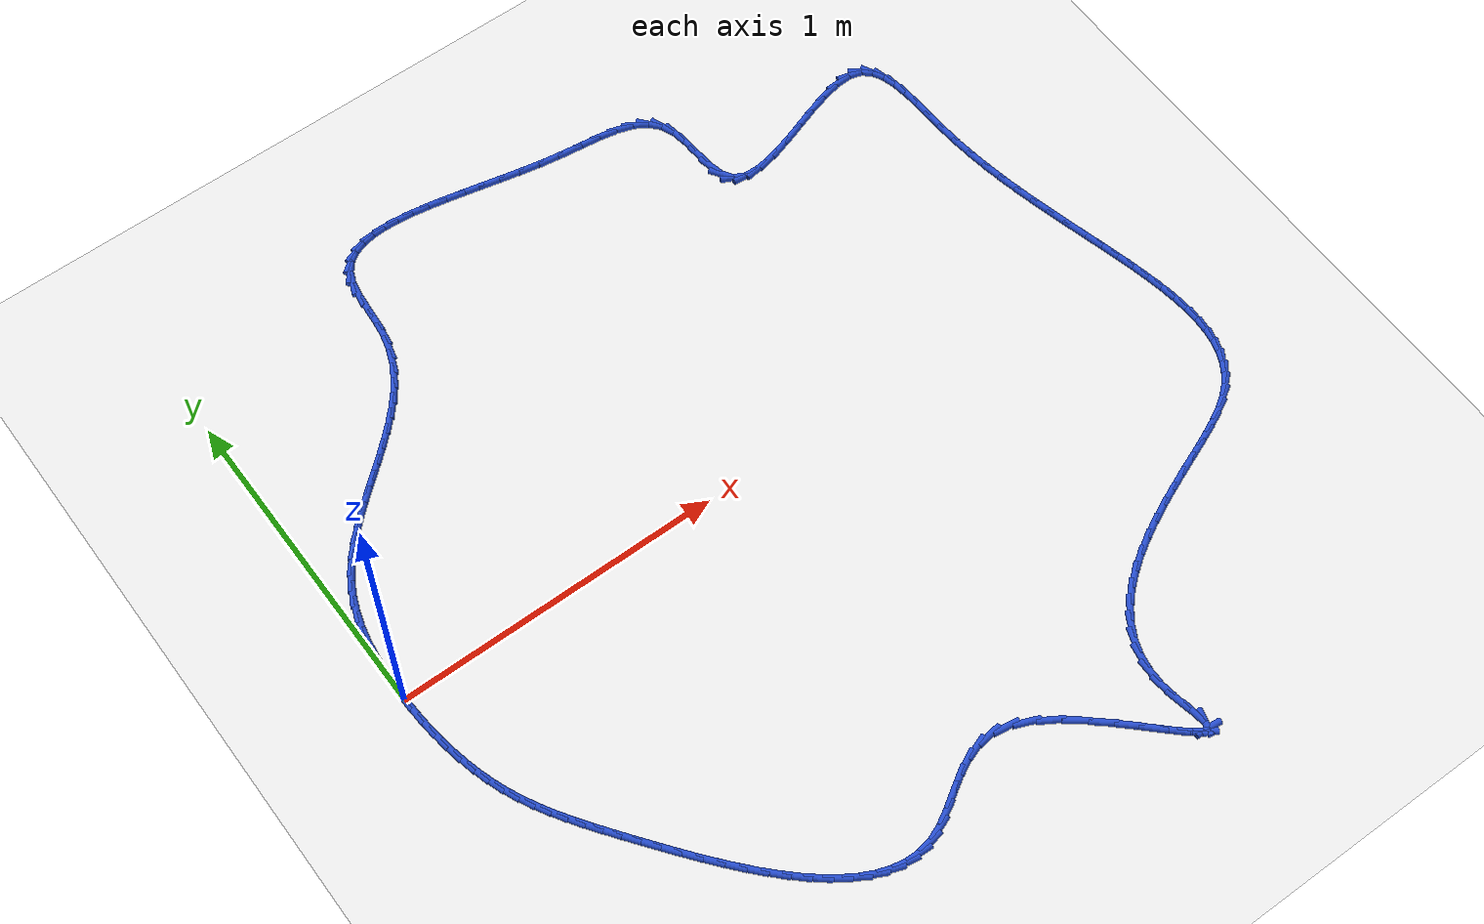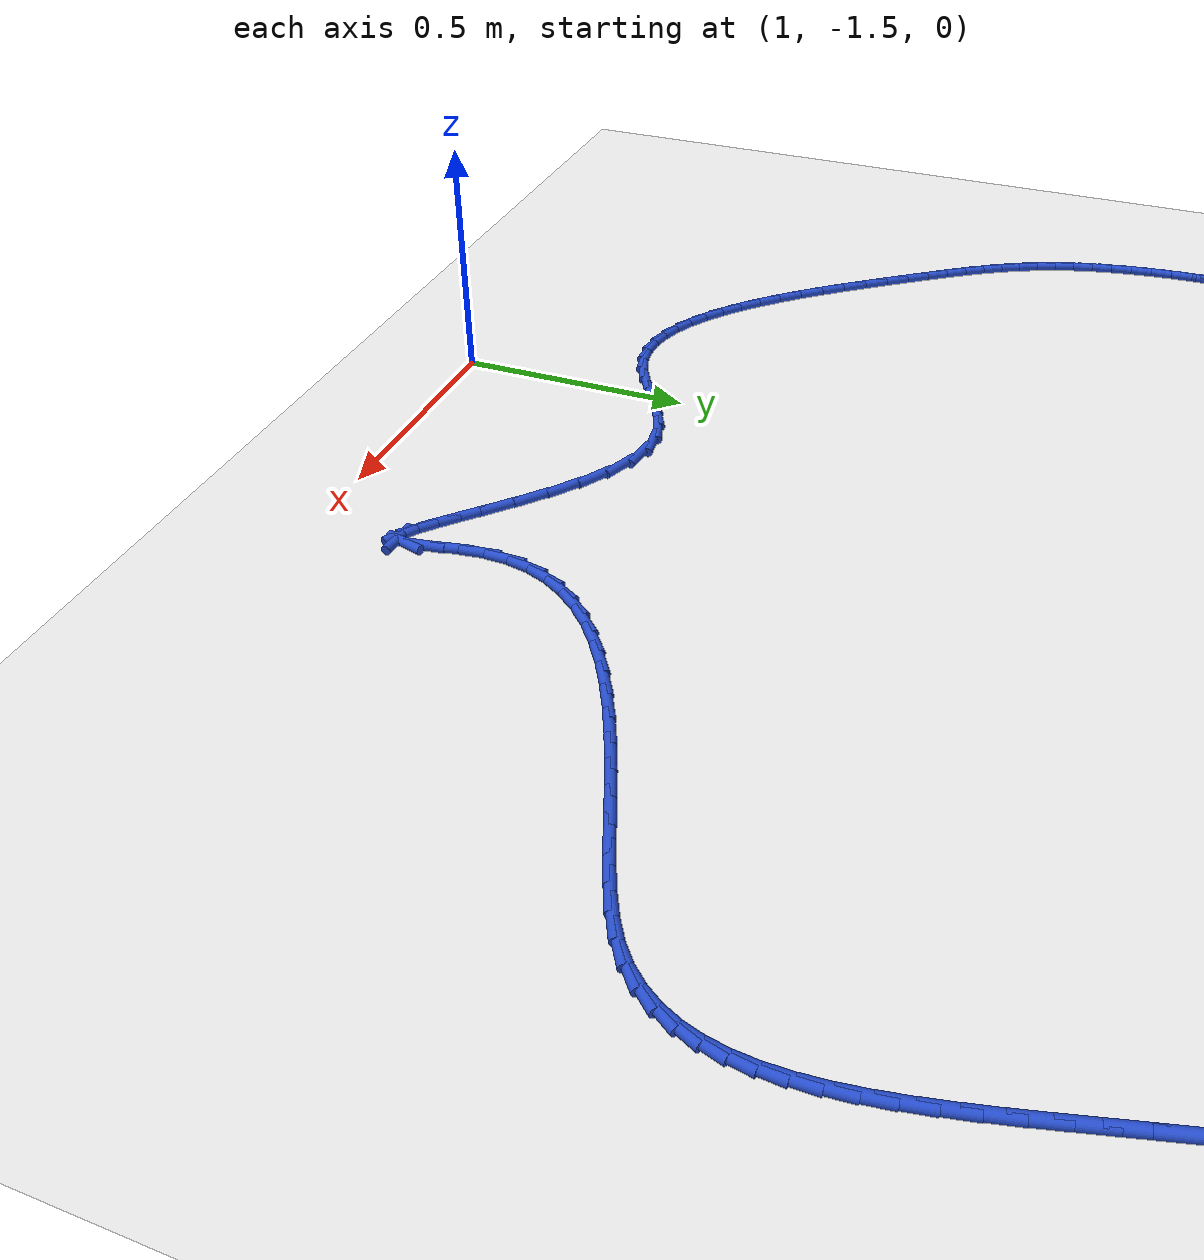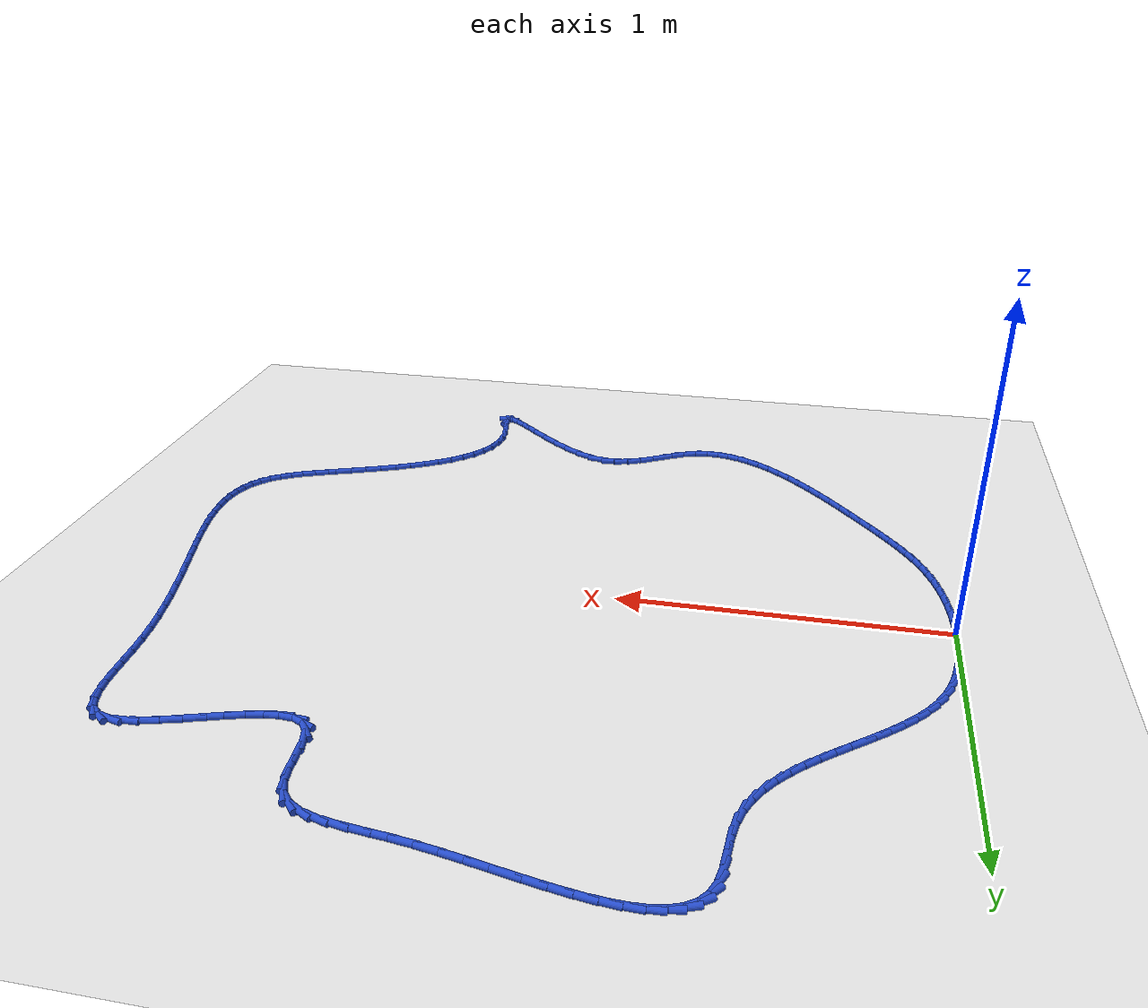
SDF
<sdf version="1.6">
 <world name="default">
  <light name="sun" type="directional">
   <pose>0 0 10 0 -0 0</pose>
   <diffuse>0.8 0.8 0.8 1</diffuse>
   <specular>0.2 0.2 0.2 1</specular>
   <attenuation>
    <range>1000</range>
    <constant>0.9</constant>
    <linear>0.01</linear>
    <quadratic>0.001</quadratic>
   </attenuation>
   <direction>-0.5 0.1 -0.9</direction>
  </light>
  <model name="ground_plane">
   <static>1</static>
   <link name="link">
    <collision name="collision">
     <geometry><plane><normal>0 0 1</normal><size>100 100</size></plane></geometry>
     <surface><friction><ode><mu>100</mu><mu2>50</mu2></ode></friction></surface>
    </collision>
    <visual name="visual">
     <cast_shadows>0</cast_shadows>
     <geometry><plane><normal>0 0 1</normal><size>100 100</size></plane></geometry>
     <material>
      <script><uri>file://media/materials/scripts/gazebo.material</uri><name>Gazebo/WhiteGlow</name></script>
     </material>
    </visual>
   </link>
  </model>
  <gravity>0 0 -9.8</gravity>
  <magnetic_field>6e-06 2.3e-05 -4.2e-05</magnetic_field>
  <atmosphere type="adiabatic"/>
  <physics name="default_physics" default="0" type="ode">
   <max_step_size>0.001</max_step_size>
   <real_time_factor>1</real_time_factor>
   <real_time_update_rate>1000</real_time_update_rate>
  </physics>
  <scene><ambient>0.4 0.4 0.4 1</ambient><background>0.7 0.7 0.7 1</background><shadows>1</shadows></scene>
  <spherical_coordinates>
   <surface_model>EARTH_WGS84</surface_model>
   <latitude_deg>0</latitude_deg>
   <longitude_deg>0</longitude_deg>
   <elevation>0</elevation>
   <heading_deg>0</heading_deg>
  </spherical_coordinates>
  <model name="line">
   <link name="link_0">
    <pose>-1.9949319973733282e-17 -1.3877787807814457e-17 0.01 0 1.57 -1.5624615225826253</pose>
    <collision name="collision">
     <geometry><cylinder><radius>0.01</radius><length>0.08</length></cylinder></geometry>
    </collision>
    <visual name="visual">
     <material>
      <script><name>Gazebo/Blue</name><uri>file://media/materials/scripts/gazebo.material</uri></script>
     </material>
     <geometry><cylinder><radius>0.01</radius><length>0.08</length></cylinder></geometry>
    </visual>
   </link>
   <link name="link_1">
    <pose>-0.0004156470203592439 0.04986768553568635 0.01 0 1.57 1.537246426346171</pose>
    <collision name="collision">
     <geometry><cylinder><radius>0.01</radius><length>0.08</length></cylinder></geometry>
    </collision>
    <visual name="visual">
     <material>
      <script><name>Gazebo/Blue</name><uri>file://media/materials/scripts/gazebo.material</uri></script>
     </material>
     <geometry><cylinder><radius>0.01</radius><length>0.08</length></cylinder></geometry>
    </visual>
   </link>
   <link name="link_2">
    <pose>0.0012534649457446988 0.09959914966241958 0.01 0 1.57 1.4872726742245124</pose>
    <collision name="collision">
     <geometry><cylinder><radius>0.01</radius><length>0.08</length></cylinder></geometry>
    </collision>
    <visual name="visual">
     <material>
      <script><name>Gazebo/Blue</name><uri>file://media/materials/scripts/gazebo.material</uri></script>
     </material>
     <geometry><cylinder><radius>0.01</radius><length>0.08</length></cylinder></geometry>
    </visual>
   </link>
   <link name="link_3">
    <pose>0.005376136604858719 0.14884364759202498 0.01 0 1.57 1.4282964904165913</pose>
    <collision name="collision">
     <geometry><cylinder><radius>0.01</radius><length>0.08</length></cylinder></geometry>
    </collision>
    <visual name="visual">
     <material>
      <script><name>Gazebo/Blue</name><uri>file://media/materials/scripts/gazebo.material</uri></script>
     </material>
     <geometry><cylinder><radius>0.01</radius><length>0.08</length></cylinder></geometry>
    </visual>
   </link>
   <link name="link_4">
    <pose>0.012321168663529738 0.19725043453632796 0.01 0 1.57 1.359338968343592</pose>
    <collision name="collision">
     <geometry><cylinder><radius>0.01</radius><length>0.08</length></cylinder></geometry>
    </collision>
    <visual name="visual">
     <material>
      <script><name>Gazebo/Blue</name><uri>file://media/materials/scripts/gazebo.material</uri></script>
     </material>
     <geometry><cylinder><radius>0.01</radius><length>0.08</length></cylinder></geometry>
    </visual>
   </link>
   <link name="link_5">
    <pose>0.022457361828304667 0.24446876570715387 0.01 0 1.57 1.2794918623715765</pose>
    <collision name="collision">
     <geometry><cylinder><radius>0.01</radius><length>0.08</length></cylinder></geometry>
    </collision>
    <visual name="visual">
     <material>
      <script><name>Gazebo/Blue</name><uri>file://media/materials/scripts/gazebo.material</uri></script>
     </material>
     <geometry><cylinder><radius>0.01</radius><length>0.08</length></cylinder></geometry>
    </visual>
   </link>
   <link name="link_6">
    <pose>0.036153516805730423 0.2901478963163279 0.01 0 1.57 1.1881411486129976</pose>
    <collision name="collision">
     <geometry><cylinder><radius>0.01</radius><length>0.08</length></cylinder></geometry>
    </collision>
    <visual name="visual">
     <material>
      <script><name>Gazebo/Blue</name><uri>file://media/materials/scripts/gazebo.material</uri></script>
     </material>
     <geometry><cylinder><radius>0.01</radius><length>0.08</length></cylinder></geometry>
    </visual>
   </link>
   <link name="link_7">
    <pose>0.05377843430235392 0.3339370815756756 0.01 0 1.57 1.085473252741672</pose>
    <collision name="collision">
     <geometry><cylinder><radius>0.01</radius><length>0.08</length></cylinder></geometry>
    </collision>
    <visual name="visual">
     <material>
      <script><name>Gazebo/Blue</name><uri>file://media/materials/scripts/gazebo.material</uri></script>
     </material>
     <geometry><cylinder><radius>0.01</radius><length>0.08</length></cylinder></geometry>
    </visual>
   </link>
   <link name="link_8">
    <pose>0.07569360500619322 0.3754906586780467 0.01 0 1.57 0.9825776368577154</pose>
    <collision name="collision">
     <geometry><cylinder><radius>0.01</radius><length>0.08</length></cylinder></geometry>
    </collision>
    <visual name="visual">
     <material>
      <script><name>Gazebo/Blue</name><uri>file://media/materials/scripts/gazebo.material</uri></script>
     </material>
     <geometry><cylinder><radius>0.01</radius><length>0.08</length></cylinder></geometry>
    </visual>
   </link>
   <link name="link_9">
    <pose>0.10186889865802944 0.41473522270658336 0.01 0 1.57 0.8958794211879014</pose>
    <collision name="collision">
     <geometry><cylinder><radius>0.01</radius><length>0.08</length></cylinder></geometry>
    </collision>
    <visual name="visual">
     <material>
      <script><name>Gazebo/Blue</name><uri>file://media/materials/scripts/gazebo.material</uri></script>
     </material>
     <geometry><cylinder><radius>0.01</radius><length>0.08</length></cylinder></geometry>
    </visual>
   </link>
   <link name="link_10">
    <pose>0.1316927472945343 0.4520015887019509 0.01 0 1.57 0.8268269276010971</pose>
    <collision name="collision">
     <geometry><cylinder><radius>0.01</radius><length>0.08</length></cylinder></geometry>
    </collision>
    <visual name="visual">
     <material>
      <script><name>Gazebo/Blue</name><uri>file://media/materials/scripts/gazebo.material</uri></script>
     </material>
     <geometry><cylinder><radius>0.01</radius><length>0.08</length></cylinder></geometry>
    </visual>
   </link>
   <link name="link_11">
    <pose>0.1645064409252646 0.48765334520413034 0.01 0 1.57 0.7746992108108078</pose>
    <collision name="collision">
     <geometry><cylinder><radius>0.01</radius><length>0.08</length></cylinder></geometry>
    </collision>
    <visual name="visual">
     <material>
      <script><name>Gazebo/Blue</name><uri>file://media/materials/scripts/gazebo.material</uri></script>
     </material>
     <geometry><cylinder><radius>0.01</radius><length>0.08</length></cylinder></geometry>
    </visual>
   </link>
   <link name="link_12">
    <pose>0.19965126955977727 0.5220540807531029 0.01 0 1.57 0.738455221369678</pose>
    <collision name="collision">
     <geometry><cylinder><radius>0.01</radius><length>0.08</length></cylinder></geometry>
    </collision>
    <visual name="visual">
     <material>
      <script><name>Gazebo/Blue</name><uri>file://media/materials/scripts/gazebo.material</uri></script>
     </material>
     <geometry><cylinder><radius>0.01</radius><length>0.08</length></cylinder></geometry>
    </visual>
   </link>
   <link name="link_13">
    <pose>0.23646852320762904 0.5555673838888494 0.01 0 1.57 0.7171411883246047</pose>
    <collision name="collision">
     <geometry><cylinder><radius>0.01</radius><length>0.08</length></cylinder></geometry>
    </collision>
    <visual name="visual">
     <material>
      <script><name>Gazebo/Blue</name><uri>file://media/materials/scripts/gazebo.material</uri></script>
     </material>
     <geometry><cylinder><radius>0.01</radius><length>0.08</length></cylinder></geometry>
    </visual>
   </link>
   <link name="link_14">
    <pose>0.2742994918783767 0.5885568431513512 0.01 0 1.57 0.7101094055200052</pose>
    <collision name="collision">
     <geometry><cylinder><radius>0.01</radius><length>0.08</length></cylinder></geometry>
    </collision>
    <visual name="visual">
     <material>
      <script><name>Gazebo/Blue</name><uri>file://media/materials/scripts/gazebo.material</uri></script>
     </material>
     <geometry><cylinder><radius>0.01</radius><length>0.08</length></cylinder></geometry>
    </visual>
   </link>
   <link name="link_15">
    <pose>0.31248546558157725 0.6213860470805893 0.01 0 1.57 0.7171163417923704</pose>
    <collision name="collision">
     <geometry><cylinder><radius>0.01</radius><length>0.08</length></cylinder></geometry>
    </collision>
    <visual name="visual">
     <material>
      <script><name>Gazebo/Blue</name><uri>file://media/materials/scripts/gazebo.material</uri></script>
     </material>
     <geometry><cylinder><radius>0.01</radius><length>0.08</length></cylinder></geometry>
    </visual>
   </link>
   <link name="link_16">
    <pose>0.3503677343267876 0.6544185842165452 0.01 0 1.57 0.7383480109168092</pose>
    <collision name="collision">
     <geometry><cylinder><radius>0.01</radius><length>0.08</length></cylinder></geometry>
    </collision>
    <visual name="visual">
     <material>
      <script><name>Gazebo/Blue</name><uri>file://media/materials/scripts/gazebo.material</uri></script>
     </material>
     <geometry><cylinder><radius>0.01</radius><length>0.08</length></cylinder></geometry>
    </visual>
   </link>
   <link name="link_17">
    <pose>0.3872875881235644 0.6880180430991996 0.01 0 1.57 0.7743893854324299</pose>
    <collision name="collision">
     <geometry><cylinder><radius>0.01</radius><length>0.08</length></cylinder></geometry>
    </collision>
    <visual name="visual">
     <material>
      <script><name>Gazebo/Blue</name><uri>file://media/materials/scripts/gazebo.material</uri></script>
     </material>
     <geometry><cylinder><radius>0.01</radius><length>0.08</length></cylinder></geometry>
    </visual>
   </link>
   <link name="link_18">
    <pose>0.42258631698146454 0.7225480122685337 0.01 0 1.57 0.8261230684143543</pose>
    <collision name="collision">
     <geometry><cylinder><radius>0.01</radius><length>0.08</length></cylinder></geometry>
    </collision>
    <visual name="visual">
     <material>
      <script><name>Gazebo/Blue</name><uri>file://media/materials/scripts/gazebo.material</uri></script>
     </material>
     <geometry><cylinder><radius>0.01</radius><length>0.08</length></cylinder></geometry>
    </visual>
   </link>
   <link name="link_19">
    <pose>0.4556052109100448 0.7583720802645288 0.01 0 1.57 0.8945127239587646</pose>
    <collision name="collision">
     <geometry><cylinder><radius>0.01</radius><length>0.08</length></cylinder></geometry>
    </collision>
    <visual name="visual">
     <material>
      <script><name>Gazebo/Blue</name><uri>file://media/materials/scripts/gazebo.material</uri></script>
     </material>
     <geometry><cylinder><radius>0.01</radius><length>0.08</length></cylinder></geometry>
    </visual>
   </link>
   <link name="link_20">
    <pose>0.4856855599188623 0.7958538356271662 0.01 0 1.57 0.9802089847060115</pose>
    <collision name="collision">
     <geometry><cylinder><radius>0.01</radius><length>0.08</length></cylinder></geometry>
    </collision>
    <visual name="visual">
     <material>
      <script><name>Gazebo/Blue</name><uri>file://media/materials/scripts/gazebo.material</uri></script>
     </material>
     <geometry><cylinder><radius>0.01</radius><length>0.08</length></cylinder></geometry>
    </visual>
   </link>
   <link name="link_21">
    <pose>0.5121686540174738 0.8353568668964265 0.01 0 1.57 1.0829431447188298</pose>
    <collision name="collision">
     <geometry><cylinder><radius>0.01</radius><length>0.08</length></cylinder></geometry>
    </collision>
    <visual name="visual">
     <material>
      <script><name>Gazebo/Blue</name><uri>file://media/materials/scripts/gazebo.material</uri></script>
     </material>
     <geometry><cylinder><radius>0.01</radius><length>0.08</length></cylinder></geometry>
    </visual>
   </link>
   <link name="link_22">
    <pose>0.5343957832154358 0.877244762612291 0.01 0 1.57 1.2008029678384557</pose>
    <collision name="collision">
     <geometry><cylinder><radius>0.01</radius><length>0.08</length></cylinder></geometry>
    </collision>
    <visual name="visual">
     <material>
      <script><name>Gazebo/Blue</name><uri>file://media/materials/scripts/gazebo.material</uri></script>
     </material>
     <geometry><cylinder><radius>0.01</radius><length>0.08</length></cylinder></geometry>
    </visual>
   </link>
   <link name="link_23">
    <pose>0.5517082375223056 0.9218811113147412 0.01 0 1.57 1.3297051357754062</pose>
    <collision name="collision">
     <geometry><cylinder><radius>0.01</radius><length>0.08</length></cylinder></geometry>
    </collision>
    <visual name="visual">
     <material>
      <script><name>Gazebo/Blue</name><uri>file://media/materials/scripts/gazebo.material</uri></script>
     </material>
     <geometry><cylinder><radius>0.01</radius><length>0.08</length></cylinder></geometry>
    </visual>
   </link>
   <link name="link_24">
    <pose>0.5634481354967837 0.9696288172080912 0.01 0 1.57 1.4455127388908906</pose>
    <collision name="collision">
     <geometry><cylinder><radius>0.01</radius><length>0.08</length></cylinder></geometry>
    </collision>
    <visual name="visual">
     <material>
      <script><name>Gazebo/Blue</name><uri>file://media/materials/scripts/gazebo.material</uri></script>
     </material>
     <geometry><cylinder><radius>0.01</radius><length>0.08</length></cylinder></geometry>
    </visual>
   </link>
   <link name="link_25">
    <pose>0.5698104761728964 1.020146352498578 0.01 0 1.57 1.4993683478524291</pose>
    <collision name="collision">
     <geometry><cylinder><radius>0.01</radius><length>0.08</length></cylinder></geometry>
    </collision>
    <visual name="visual">
     <material>
      <script><name>Gazebo/Blue</name><uri>file://media/materials/scripts/gazebo.material</uri></script>
     </material>
     <geometry><cylinder><radius>0.01</radius><length>0.08</length></cylinder></geometry>
    </visual>
   </link>
   <link name="link_26">
    <pose>0.5734531856451275 1.0710579481587523 0.01 0 1.57 1.4881480987408857</pose>
    <collision name="collision">
     <geometry><cylinder><radius>0.01</radius><length>0.08</length></cylinder></geometry>
    </collision>
    <visual name="visual">
     <material>
      <script><name>Gazebo/Blue</name><uri>file://media/materials/scripts/gazebo.material</uri></script>
     </material>
     <geometry><cylinder><radius>0.01</radius><length>0.08</length></cylinder></geometry>
    </visual>
   </link>
   <link name="link_27">
    <pose>0.5774761488320804 1.119622801669897 0.01 0 1.57 1.399904449243594</pose>
    <collision name="collision">
     <geometry><cylinder><radius>0.01</radius><length>0.08</length></cylinder></geometry>
    </collision>
    <visual name="visual">
     <material>
      <script><name>Gazebo/Blue</name><uri>file://media/materials/scripts/gazebo.material</uri></script>
     </material>
     <geometry><cylinder><radius>0.01</radius><length>0.08</length></cylinder></geometry>
    </visual>
   </link>
   <link name="link_28">
    <pose>0.584979250652358 1.163100110513294 0.01 0 1.57 1.2007088045246785</pose>
    <collision name="collision">
     <geometry><cylinder><radius>0.01</radius><length>0.08</length></cylinder></geometry>
    </collision>
    <visual name="visual">
     <material>
      <script><name>Gazebo/Blue</name><uri>file://media/materials/scripts/gazebo.material</uri></script>
     </material>
     <geometry><cylinder><radius>0.01</radius><length>0.08</length></cylinder></geometry>
    </visual>
   </link>
   <link name="link_29">
    <pose>0.5988777635229073 1.1989243573524517 0.01 0 1.57 0.9186172230731402</pose>
    <collision name="collision">
     <geometry><cylinder><radius>0.01</radius><length>0.08</length></cylinder></geometry>
    </collision>
    <visual name="visual">
     <material>
      <script><name>Gazebo/Blue</name><uri>file://media/materials/scripts/gazebo.material</uri></script>
     </material>
     <geometry><cylinder><radius>0.01</radius><length>0.08</length></cylinder></geometry>
    </visual>
   </link>
   <link name="link_30">
    <pose>0.6199679305519616 1.2265419928117929 0.01 0 1.57 0.6283411581405366</pose>
    <collision name="collision">
     <geometry><cylinder><radius>0.01</radius><length>0.08</length></cylinder></geometry>
    </collision>
    <visual name="visual">
     <material>
      <script><name>Gazebo/Blue</name><uri>file://media/materials/scripts/gazebo.material</uri></script>
     </material>
     <geometry><cylinder><radius>0.01</radius><length>0.08</length></cylinder></geometry>
    </visual>
   </link>
   <link name="link_31">
    <pose>0.6476916340469651 1.2466854009039725 0.01 0 1.57 0.37824850765023066</pose>
    <collision name="collision">
     <geometry><cylinder><radius>0.01</radius><length>0.08</length></cylinder></geometry>
    </collision>
    <visual name="visual">
     <material>
      <script><name>Gazebo/Blue</name><uri>file://media/materials/scripts/gazebo.material</uri></script>
     </material>
     <geometry><cylinder><radius>0.01</radius><length>0.08</length></cylinder></geometry>
    </visual>
   </link>
   <link name="link_32">
    <pose>0.6814687498241567 1.2601078602819642 0.01 0 1.57 0.1876934036571288</pose>
    <collision name="collision">
     <geometry><cylinder><radius>0.01</radius><length>0.08</length></cylinder></geometry>
    </collision>
    <visual name="visual">
     <material>
      <script><name>Gazebo/Blue</name><uri>file://media/materials/scripts/gazebo.material</uri></script>
     </material>
     <geometry><cylinder><radius>0.01</radius><length>0.08</length></cylinder></geometry>
    </visual>
   </link>
   <link name="link_33">
    <pose>0.7207191536997767 1.2675626495987433 0.01 0 1.57 0.05070902438882522</pose>
    <collision name="collision">
     <geometry><cylinder><radius>0.01</radius><length>0.08</length></cylinder></geometry>
    </collision>
    <visual name="visual">
     <material>
      <script><name>Gazebo/Blue</name><uri>file://media/materials/scripts/gazebo.material</uri></script>
     </material>
     <geometry><cylinder><radius>0.01</radius><length>0.08</length></cylinder></geometry>
    </visual>
   </link>
   <link name="link_34">
    <pose>0.7648627214900647 1.2698030475072835 0.01 0 1.57 -0.04579689335121554</pose>
    <collision name="collision">
     <geometry><cylinder><radius>0.01</radius><length>0.08</length></cylinder></geometry>
    </collision>
    <visual name="visual">
     <material>
      <script><name>Gazebo/Blue</name><uri>file://media/materials/scripts/gazebo.material</uri></script>
     </material>
     <geometry><cylinder><radius>0.01</radius><length>0.08</length></cylinder></geometry>
    </visual>
   </link>
   <link name="link_35">
    <pose>0.81331932901126 1.2675823326605593 0.01 0 1.57 -0.11311165987841174</pose>
    <collision name="collision">
     <geometry><cylinder><radius>0.01</radius><length>0.08</length></cylinder></geometry>
    </collision>
    <visual name="visual">
     <material>
      <script><name>Gazebo/Blue</name><uri>file://media/materials/scripts/gazebo.material</uri></script>
     </material>
     <geometry><cylinder><radius>0.01</radius><length>0.08</length></cylinder></geometry>
    </visual>
   </link>
   <link name="link_36">
    <pose>0.8655088520796029 1.2616537837115451 0.01 0 1.57 -0.15915442153044063</pose>
    <collision name="collision">
     <geometry><cylinder><radius>0.01</radius><length>0.08</length></cylinder></geometry>
    </collision>
    <visual name="visual">
     <material>
      <script><name>Gazebo/Blue</name><uri>file://media/materials/scripts/gazebo.material</uri></script>
     </material>
     <geometry><cylinder><radius>0.01</radius><length>0.08</length></cylinder></geometry>
    </visual>
   </link>
   <link name="link_37">
    <pose>0.920851166511333 1.2527706793132154 0.01 0 1.57 -0.18910372058178332</pose>
    <collision name="collision">
     <geometry><cylinder><radius>0.01</radius><length>0.08</length></cylinder></geometry>
    </collision>
    <visual name="visual">
     <material>
      <script><name>Gazebo/Blue</name><uri>file://media/materials/scripts/gazebo.material</uri></script>
     </material>
     <geometry><cylinder><radius>0.01</radius><length>0.08</length></cylinder></geometry>
    </visual>
   </link>
   <link name="link_38">
    <pose>0.9787661481226895 1.2416862981185441 0.01 0 1.57 -0.206221466034016</pose>
    <collision name="collision">
     <geometry><cylinder><radius>0.01</radius><length>0.08</length></cylinder></geometry>
    </collision>
    <visual name="visual">
     <material>
      <script><name>Gazebo/Blue</name><uri>file://media/materials/scripts/gazebo.material</uri></script>
     </material>
     <geometry><cylinder><radius>0.01</radius><length>0.08</length></cylinder></geometry>
    </visual>
   </link>
   <link name="link_39">
    <pose>1.0386736727299128 1.229153918780506 0.01 0 1.57 -0.2124511669112916</pose>
    <collision name="collision">
     <geometry><cylinder><radius>0.01</radius><length>0.08</length></cylinder></geometry>
    </collision>
    <visual name="visual">
     <material>
      <script><name>Gazebo/Blue</name><uri>file://media/materials/scripts/gazebo.material</uri></script>
     </material>
     <geometry><cylinder><radius>0.01</radius><length>0.08</length></cylinder></geometry>
    </visual>
   </link>
   <link name="link_40">
    <pose>1.0999936161492425 1.2159268199520756 0.01 0 1.57 -0.20878784738946346</pose>
    <collision name="collision">
     <geometry><cylinder><radius>0.01</radius><length>0.08</length></cylinder></geometry>
    </collision>
    <visual name="visual">
     <material>
      <script><name>Gazebo/Blue</name><uri>file://media/materials/scripts/gazebo.material</uri></script>
     </material>
     <geometry><cylinder><radius>0.01</radius><length>0.08</length></cylinder></geometry>
    </visual>
   </link>
   <link name="link_41">
    <pose>1.162145854196918 1.202758280286227 0.01 0 1.57 -0.1954814440411361</pose>
    <collision name="collision">
     <geometry><cylinder><radius>0.01</radius><length>0.08</length></cylinder></geometry>
    </collision>
    <visual name="visual">
     <material>
      <script><name>Gazebo/Blue</name><uri>file://media/materials/scripts/gazebo.material</uri></script>
     </material>
     <geometry><cylinder><radius>0.01</radius><length>0.08</length></cylinder></geometry>
    </visual>
   </link>
   <link name="link_42">
    <pose>1.2245502626891793 1.1904015784359347 0.01 0 1.57 -0.17212326842430617</pose>
    <collision name="collision">
     <geometry><cylinder><radius>0.01</radius><length>0.08</length></cylinder></geometry>
    </collision>
    <visual name="visual">
     <material>
      <script><name>Gazebo/Blue</name><uri>file://media/materials/scripts/gazebo.material</uri></script>
     </material>
     <geometry><cylinder><radius>0.01</radius><length>0.08</length></cylinder></geometry>
    </visual>
   </link>
   <link name="link_43">
    <pose>1.2866267174422656 1.1796099930541732 0.01 0 1.57 -0.13861630444678202</pose>
    <collision name="collision">
     <geometry><cylinder><radius>0.01</radius><length>0.08</length></cylinder></geometry>
    </collision>
    <visual name="visual">
     <material>
      <script><name>Gazebo/Blue</name><uri>file://media/materials/scripts/gazebo.material</uri></script>
     </material>
     <geometry><cylinder><radius>0.01</radius><length>0.08</length></cylinder></geometry>
    </visual>
   </link>
   <link name="link_44">
    <pose>1.3477766139102931 1.1710789101612555 0.01 0 1.57 -0.11695335978422734</pose>
    <collision name="collision">
     <geometry><cylinder><radius>0.01</radius><length>0.08</length></cylinder></geometry>
    </collision>
    <visual name="visual">
     <material>
      <script><name>Gazebo/Blue</name><uri>file://media/materials/scripts/gazebo.material</uri></script>
     </material>
     <geometry><cylinder><radius>0.01</radius><length>0.08</length></cylinder></geometry>
    </visual>
   </link>
   <link name="link_45">
    <pose>1.4069613404930985 1.1641253246729195 0.01 0 1.57 -0.1331339041285381</pose>
    <collision name="collision">
     <geometry><cylinder><radius>0.01</radius><length>0.08</length></cylinder></geometry>
    </collision>
    <visual name="visual">
     <material>
      <script><name>Gazebo/Blue</name><uri>file://media/materials/scripts/gazebo.material</uri></script>
     </material>
     <geometry><cylinder><radius>0.01</radius><length>0.08</length></cylinder></geometry>
    </visual>
   </link>
   <link name="link_46">
    <pose>1.4626938041079651 1.1566612929246938 0.01 0 1.57 -0.19684701664099774</pose>
    <collision name="collision">
     <geometry><cylinder><radius>0.01</radius><length>0.08</length></cylinder></geometry>
    </collision>
    <visual name="visual">
     <material>
      <script><name>Gazebo/Blue</name><uri>file://media/materials/scripts/gazebo.material</uri></script>
     </material>
     <geometry><cylinder><radius>0.01</radius><length>0.08</length></cylinder></geometry>
    </visual>
   </link>
   <link name="link_47">
    <pose>1.5134667362310386 1.146535668518596 0.01 0 1.57 -0.32519277962173165</pose>
    <collision name="collision">
     <geometry><cylinder><radius>0.01</radius><length>0.08</length></cylinder></geometry>
    </collision>
    <visual name="visual">
     <material>
      <script><name>Gazebo/Blue</name><uri>file://media/materials/scripts/gazebo.material</uri></script>
     </material>
     <geometry><cylinder><radius>0.01</radius><length>0.08</length></cylinder></geometry>
    </visual>
   </link>
   <link name="link_48">
    <pose>1.557772868338464 1.1315973050566435 0.01 0 1.57 -0.5425016413661428</pose>
    <collision name="collision">
     <geometry><cylinder><radius>0.01</radius><length>0.08</length></cylinder></geometry>
    </collision>
    <visual name="visual">
     <material>
      <script><name>Gazebo/Blue</name><uri>file://media/materials/scripts/gazebo.material</uri></script>
     </material>
     <geometry><cylinder><radius>0.01</radius><length>0.08</length></cylinder></geometry>
    </visual>
   </link>
   <link name="link_49">
    <pose>1.5941049319063882 1.1096950561408547 0.01 0 1.57 -0.8572751255862286</pose>
    <collision name="collision">
     <geometry><cylinder><radius>0.01</radius><length>0.08</length></cylinder></geometry>
    </collision>
    <visual name="visual">
     <material>
      <script><name>Gazebo/Blue</name><uri>file://media/materials/scripts/gazebo.material</uri></script>
     </material>
     <geometry><cylinder><radius>0.01</radius><length>0.08</length></cylinder></geometry>
    </visual>
   </link>
   <link name="link_50">
    <pose>1.6209556584109568 1.0786777753732462 0.01 0 1.57 -1.203652902772793</pose>
    <collision name="collision">
     <geometry><cylinder><radius>0.01</radius><length>0.08</length></cylinder></geometry>
    </collision>
    <visual name="visual">
     <material>
      <script><name>Gazebo/Blue</name><uri>file://media/materials/scripts/gazebo.material</uri></script>
     </material>
     <geometry><cylinder><radius>0.01</radius><length>0.08</length></cylinder></geometry>
    </visual>
   </link>
   <link name="link_51">
    <pose>1.6370884244367263 1.0367287763948025 0.01 0 1.57 -1.4203550233422715</pose>
    <collision name="collision">
     <geometry><cylinder><radius>0.01</radius><length>0.08</length></cylinder></geometry>
    </collision>
    <visual name="visual">
     <material>
      <script><name>Gazebo/Blue</name><uri>file://media/materials/scripts/gazebo.material</uri></script>
     </material>
     <geometry><cylinder><radius>0.01</radius><length>0.08</length></cylinder></geometry>
    </visual>
   </link>
   <link name="link_52">
    <pose>1.6447308638454186 0.9863124612087226 0.01 0 1.57 -1.5002855942289508</pose>
    <collision name="collision">
     <geometry><cylinder><radius>0.01</radius><length>0.08</length></cylinder></geometry>
    </collision>
    <visual name="visual">
     <material>
      <script><name>Gazebo/Blue</name><uri>file://media/materials/scripts/gazebo.material</uri></script>
     </material>
     <geometry><cylinder><radius>0.01</radius><length>0.08</length></cylinder></geometry>
    </visual>
   </link>
   <link name="link_53">
    <pose>1.6485065140761337 0.9328540612547847 0.01 0 1.57 -1.4812565143868008</pose>
    <collision name="collision">
     <geometry><cylinder><radius>0.01</radius><length>0.08</length></cylinder></geometry>
    </collision>
    <visual name="visual">
     <material>
      <script><name>Gazebo/Blue</name><uri>file://media/materials/scripts/gazebo.material</uri></script>
     </material>
     <geometry><cylinder><radius>0.01</radius><length>0.08</length></cylinder></geometry>
    </visual>
   </link>
   <link name="link_54">
    <pose>1.6530867377218688 0.8818379097349569 0.01 0 1.57 -1.3415219892443728</pose>
    <collision name="collision">
     <geometry><cylinder><radius>0.01</radius><length>0.08</length></cylinder></geometry>
    </collision>
    <visual name="visual">
     <material>
      <script><name>Gazebo/Blue</name><uri>file://media/materials/scripts/gazebo.material</uri></script>
     </material>
     <geometry><cylinder><radius>0.01</radius><length>0.08</length></cylinder></geometry>
    </visual>
   </link>
   <link name="link_55">
    <pose>1.6631428973756195 0.8387483398512072 0.01 0 1.57 -0.9790302515035469</pose>
    <collision name="collision">
     <geometry><cylinder><radius>0.01</radius><length>0.08</length></cylinder></geometry>
    </collision>
    <visual name="visual">
     <material>
      <script><name>Gazebo/Blue</name><uri>file://media/materials/scripts/gazebo.material</uri></script>
     </material>
     <geometry><cylinder><radius>0.01</radius><length>0.08</length></cylinder></geometry>
    </visual>
   </link>
   <link name="link_56">
    <pose>1.6832052617548636 0.8088988053950726 0.01 0 1.57 -0.450450820765415</pose>
    <collision name="collision">
     <geometry><cylinder><radius>0.01</radius><length>0.08</length></cylinder></geometry>
    </collision>
    <visual name="visual">
     <material>
      <script><name>Gazebo/Blue</name><uri>file://media/materials/scripts/gazebo.material</uri></script>
     </material>
     <geometry><cylinder><radius>0.01</radius><length>0.08</length></cylinder></geometry>
    </visual>
   </link>
   <link name="link_57">
    <pose>1.7145962808699982 0.7937177568762134 0.01 0 1.57 -0.07193934047617574</pose>
    <collision name="collision">
     <geometry><cylinder><radius>0.01</radius><length>0.08</length></cylinder></geometry>
    </collision>
    <visual name="visual">
     <material>
      <script><name>Gazebo/Blue</name><uri>file://media/materials/scripts/gazebo.material</uri></script>
     </material>
     <geometry><cylinder><radius>0.01</radius><length>0.08</length></cylinder></geometry>
    </visual>
   </link>
   <link name="link_58">
    <pose>1.7554511945861502 0.7907736006418647 0.01 0 1.57 0.1376922960731505</pose>
    <collision name="collision">
     <geometry><cylinder><radius>0.01</radius><length>0.08</length></cylinder></geometry>
    </collision>
    <visual name="visual">
     <material>
      <script><name>Gazebo/Blue</name><uri>file://media/materials/scripts/gazebo.material</uri></script>
     </material>
     <geometry><cylinder><radius>0.01</radius><length>0.08</length></cylinder></geometry>
    </visual>
   </link>
   <link name="link_59">
    <pose>1.8037682706589673 0.7974688555177253 0.01 0 1.57 0.2500965880433089</pose>
    <collision name="collision">
     <geometry><cylinder><radius>0.01</radius><length>0.08</length></cylinder></geometry>
    </collision>
    <visual name="visual">
     <material>
      <script><name>Gazebo/Blue</name><uri>file://media/materials/scripts/gazebo.material</uri></script>
     </material>
     <geometry><cylinder><radius>0.01</radius><length>0.08</length></cylinder></geometry>
    </visual>
   </link>
   <link name="link_60">
    <pose>1.8575457768440962 0.8112060403294927 0.01 0 1.57 0.3075785618250034</pose>
    <collision name="collision">
     <geometry><cylinder><radius>0.01</radius><length>0.08</length></cylinder></geometry>
    </collision>
    <visual name="visual">
     <material>
      <script><name>Gazebo/Blue</name><uri>file://media/materials/scripts/gazebo.material</uri></script>
     </material>
     <geometry><cylinder><radius>0.01</radius><length>0.08</length></cylinder></geometry>
    </visual>
   </link>
   <link name="link_61">
    <pose>1.9147819808971847 0.8293876739028656 0.01 0 1.57 0.3288517925598501</pose>
    <collision name="collision">
     <geometry><cylinder><radius>0.01</radius><length>0.08</length></cylinder></geometry>
    </collision>
    <visual name="visual">
     <material>
      <script><name>Gazebo/Blue</name><uri>file://media/materials/scripts/gazebo.material</uri></script>
     </material>
     <geometry><cylinder><radius>0.01</radius><length>0.08</length></cylinder></geometry>
    </visual>
   </link>
   <link name="link_62">
    <pose>1.9734751505738795 0.8494162750635413 0.01 0 1.57 0.3201289628542197</pose>
    <collision name="collision">
     <geometry><cylinder><radius>0.01</radius><length>0.08</length></cylinder></geometry>
    </collision>
    <visual name="visual">
     <material>
      <script><name>Gazebo/Blue</name><uri>file://media/materials/scripts/gazebo.material</uri></script>
     </material>
     <geometry><cylinder><radius>0.01</radius><length>0.08</length></cylinder></geometry>
    </visual>
   </link>
   <link name="link_63">
    <pose>2.031623553629828 0.8686943626372187 0.01 0 1.57 0.2790283708326772</pose>
    <collision name="collision">
     <geometry><cylinder><radius>0.01</radius><length>0.08</length></cylinder></geometry>
    </collision>
    <visual name="visual">
     <material>
      <script><name>Gazebo/Blue</name><uri>file://media/materials/scripts/gazebo.material</uri></script>
     </material>
     <geometry><cylinder><radius>0.01</radius><length>0.08</length></cylinder></geometry>
    </visual>
   </link>
   <link name="link_64">
    <pose>2.0872254578206757 0.8846244554495951 0.01 0 1.57 0.19313328222603268</pose>
    <collision name="collision">
     <geometry><cylinder><radius>0.01</radius><length>0.08</length></cylinder></geometry>
    </collision>
    <visual name="visual">
     <material>
      <script><name>Gazebo/Blue</name><uri>file://media/materials/scripts/gazebo.material</uri></script>
     </material>
     <geometry><cylinder><radius>0.01</radius><length>0.08</length></cylinder></geometry>
    </visual>
   </link>
   <link name="link_65">
    <pose>2.138279130902072 0.8946090723263689 0.01 0 1.57 0.03238282402943888</pose>
    <collision name="collision">
     <geometry><cylinder><radius>0.01</radius><length>0.08</length></cylinder></geometry>
    </collision>
    <visual name="visual">
     <material>
      <script><name>Gazebo/Blue</name><uri>file://media/materials/scripts/gazebo.material</uri></script>
     </material>
     <geometry><cylinder><radius>0.01</radius><length>0.08</length></cylinder></geometry>
    </visual>
   </link>
   <link name="link_66">
    <pose>2.182782840629663 0.8960507320932382 0.01 0 1.57 -0.26348068863071095</pose>
    <collision name="collision">
     <geometry><cylinder><radius>0.01</radius><length>0.08</length></cylinder></geometry>
    </collision>
    <visual name="visual">
     <material>
      <script><name>Gazebo/Blue</name><uri>file://media/materials/scripts/gazebo.material</uri></script>
     </material>
     <geometry><cylinder><radius>0.01</radius><length>0.08</length></cylinder></geometry>
    </visual>
   </link>
   <link name="link_67">
    <pose>2.2187353014389175 0.886352483197996 0.01 0 1.57 -0.7084009108994147</pose>
    <collision name="collision">
     <geometry><cylinder><radius>0.01</radius><length>0.08</length></cylinder></geometry>
    </collision>
    <visual name="visual">
     <material>
      <script><name>Gazebo/Blue</name><uri>file://media/materials/scripts/gazebo.material</uri></script>
     </material>
     <geometry><cylinder><radius>0.01</radius><length>0.08</length></cylinder></geometry>
    </visual>
   </link>
   <link name="link_68">
    <pose>2.2449546755423477 0.8638889819989137 0.01 0 1.57 -1.0864813360709111</pose>
    <collision name="collision">
     <geometry><cylinder><radius>0.01</radius><length>0.08</length></cylinder></geometry>
    </collision>
    <visual name="visual">
     <material>
      <script><name>Gazebo/Blue</name><uri>file://media/materials/scripts/gazebo.material</uri></script>
     </material>
     <geometry><cylinder><radius>0.01</radius><length>0.08</length></cylinder></geometry>
    </visual>
   </link>
   <link name="link_69">
    <pose>2.26277469311391 0.8300175590394426 0.01 0 1.57 -1.3172042974333016</pose>
    <collision name="collision">
     <geometry><cylinder><radius>0.01</radius><length>0.08</length></cylinder></geometry>
    </collision>
    <visual name="visual">
     <material>
      <script><name>Gazebo/Blue</name><uri>file://media/materials/scripts/gazebo.material</uri></script>
     </material>
     <geometry><cylinder><radius>0.01</radius><length>0.08</length></cylinder></geometry>
    </visual>
   </link>
   <link name="link_70">
    <pose>2.274010192489774 0.7866659881655779 0.01 0 1.57 -1.4444528978372257</pose>
    <collision name="collision">
     <geometry><cylinder><radius>0.01</radius><length>0.08</length></cylinder></geometry>
    </collision>
    <visual name="visual">
     <material>
      <script><name>Gazebo/Blue</name><uri>file://media/materials/scripts/gazebo.material</uri></script>
     </material>
     <geometry><cylinder><radius>0.01</radius><length>0.08</length></cylinder></geometry>
    </visual>
   </link>
   <link name="link_71">
    <pose>2.2804760120061047 0.7357620432233134 0.01 0 1.57 -1.508766183994036</pose>
    <collision name="collision">
     <geometry><cylinder><radius>0.01</radius><length>0.08</length></cylinder></geometry>
    </collision>
    <visual name="visual">
     <material>
      <script><name>Gazebo/Blue</name><uri>file://media/materials/scripts/gazebo.material</uri></script>
     </material>
     <geometry><cylinder><radius>0.01</radius><length>0.08</length></cylinder></geometry>
    </visual>
   </link>
   <link name="link_72">
    <pose>2.283986989999071 0.679233498058645 0.01 0 1.57 -1.5314482749180152</pose>
    <collision name="collision">
     <geometry><cylinder><radius>0.01</radius><length>0.08</length></cylinder></geometry>
    </collision>
    <visual name="visual">
     <material>
      <script><name>Gazebo/Blue</name><uri>file://media/materials/scripts/gazebo.material</uri></script>
     </material>
     <geometry><cylinder><radius>0.01</radius><length>0.08</length></cylinder></geometry>
    </visual>
   </link>
   <link name="link_73">
    <pose>2.286357964804838 0.6190081265175664 0.01 0 1.57 -1.5217054143452202</pose>
    <collision name="collision">
     <geometry><cylinder><radius>0.01</radius><length>0.08</length></cylinder></geometry>
    </collision>
    <visual name="visual">
     <material>
      <script><name>Gazebo/Blue</name><uri>file://media/materials/scripts/gazebo.material</uri></script>
     </material>
     <geometry><cylinder><radius>0.01</radius><length>0.08</length></cylinder></geometry>
    </visual>
   </link>
   <link name="link_74">
    <pose>2.2894037747595744 0.5570137024460724 0.01 0 1.57 -1.485653239219659</pose>
    <collision name="collision">
     <geometry><cylinder><radius>0.01</radius><length>0.08</length></cylinder></geometry>
    </collision>
    <visual name="visual">
     <material>
      <script><name>Gazebo/Blue</name><uri>file://media/materials/scripts/gazebo.material</uri></script>
     </material>
     <geometry><cylinder><radius>0.01</radius><length>0.08</length></cylinder></geometry>
    </visual>
   </link>
   <link name="link_75">
    <pose>2.2946986783932077 0.49497575274910616 0.01 0 1.57 -1.4463148212602277</pose>
    <collision name="collision">
     <geometry><cylinder><radius>0.01</radius><length>0.08</length></cylinder></geometry>
    </collision>
    <visual name="visual">
     <material>
      <script><name>Gazebo/Blue</name><uri>file://media/materials/scripts/gazebo.material</uri></script>
     </material>
     <geometry><cylinder><radius>0.01</radius><length>0.08</length></cylinder></geometry>
    </visual>
   </link>
   <link name="link_76">
    <pose>2.3023999782266698 0.4334286194898496 0.01 0 1.57 -1.4122221046289114</pose>
    <collision name="collision">
     <geometry><cylinder><radius>0.01</radius><length>0.08</length></cylinder></geometry>
    </collision>
    <visual name="visual">
     <material>
      <script><name>Gazebo/Blue</name><uri>file://media/materials/scripts/gazebo.material</uri></script>
     </material>
     <geometry><cylinder><radius>0.01</radius><length>0.08</length></cylinder></geometry>
    </visual>
   </link>
   <link name="link_77">
    <pose>2.3121479687305984 0.3724720143345878 0.01 0 1.57 -1.3832988094223644</pose>
    <collision name="collision">
     <geometry><cylinder><radius>0.01</radius><length>0.08</length></cylinder></geometry>
    </collision>
    <visual name="visual">
     <material>
      <script><name>Gazebo/Blue</name><uri>file://media/materials/scripts/gazebo.material</uri></script>
     </material>
     <geometry><cylinder><radius>0.01</radius><length>0.08</length></cylinder></geometry>
    </visual>
   </link>
   <link name="link_78">
    <pose>2.323582188122727 0.3122050131945148 0.01 0 1.57 -1.359467800845129</pose>
    <collision name="collision">
     <geometry><cylinder><radius>0.01</radius><length>0.08</length></cylinder></geometry>
    </collision>
    <visual name="visual">
     <material>
      <script><name>Gazebo/Blue</name><uri>file://media/materials/scripts/gazebo.material</uri></script>
     </material>
     <geometry><cylinder><radius>0.01</radius><length>0.08</length></cylinder></geometry>
    </visual>
   </link>
   <link name="link_79">
    <pose>2.3363421746207864 0.25272669198082154 0.01 0 1.57 -1.3406879225619641</pose>
    <collision name="collision">
     <geometry><cylinder><radius>0.01</radius><length>0.08</length></cylinder></geometry>
    </collision>
    <visual name="visual">
     <material>
      <script><name>Gazebo/Blue</name><uri>file://media/materials/scripts/gazebo.material</uri></script>
     </material>
     <geometry><cylinder><radius>0.01</radius><length>0.08</length></cylinder></geometry>
    </visual>
   </link>
   <link name="link_80">
    <pose>2.3500674664425105 0.1941361266047018 0.01 0 1.57 -1.3269747535683292</pose>
    <collision name="collision">
     <geometry><cylinder><radius>0.01</radius><length>0.08</length></cylinder></geometry>
    </collision>
    <visual name="visual">
     <material>
      <script><name>Gazebo/Blue</name><uri>file://media/materials/scripts/gazebo.material</uri></script>
     </material>
     <geometry><cylinder><radius>0.01</radius><length>0.08</length></cylinder></geometry>
    </visual>
   </link>
   <link name="link_81">
    <pose>2.3643976018056287 0.13653239297734734 0.01 0 1.57 -1.3184200282570584</pose>
    <collision name="collision">
     <geometry><cylinder><radius>0.01</radius><length>0.08</length></cylinder></geometry>
    </collision>
    <visual name="visual">
     <material>
      <script><name>Gazebo/Blue</name><uri>file://media/materials/scripts/gazebo.material</uri></script>
     </material>
     <geometry><cylinder><radius>0.01</radius><length>0.08</length></cylinder></geometry>
    </visual>
   </link>
   <link name="link_82">
    <pose>2.3789721189278747 0.08001456700995037 0.01 0 1.57 -1.31521155537441</pose>
    <collision name="collision">
     <geometry><cylinder><radius>0.01</radius><length>0.08</length></cylinder></geometry>
    </collision>
    <visual name="visual">
     <material>
      <script><name>Gazebo/Blue</name><uri>file://media/materials/scripts/gazebo.material</uri></script>
     </material>
     <geometry><cylinder><radius>0.01</radius><length>0.08</length></cylinder></geometry>
    </visual>
   </link>
   <link name="link_83">
    <pose>2.3934305560269804 0.024681724613704246 0.01 0 1.57 -1.3176554393028945</pose>
    <collision name="collision">
     <geometry><cylinder><radius>0.01</radius><length>0.08</length></cylinder></geometry>
    </collision>
    <visual name="visual">
     <material>
      <script><name>Gazebo/Blue</name><uri>file://media/materials/scripts/gazebo.material</uri></script>
     </material>
     <geometry><cylinder><radius>0.01</radius><length>0.08</length></cylinder></geometry>
    </visual>
   </link>
   <link name="link_84">
    <pose>2.407412451320678 -0.029367058300199554 0.01 0 1.57 -1.3262022830353422</pose>
    <collision name="collision">
     <geometry><cylinder><radius>0.01</radius><length>0.08</length></cylinder></geometry>
    </collision>
    <visual name="visual">
     <material>
      <script><name>Gazebo/Blue</name><uri>file://media/materials/scripts/gazebo.material</uri></script>
     </material>
     <geometry><cylinder><radius>0.01</radius><length>0.08</length></cylinder></geometry>
    </visual>
   </link>
   <link name="link_85">
    <pose>2.420557343026698 -0.08203270582056749 0.01 0 1.57 -1.3414787079102308</pose>
    <collision name="collision">
     <geometry><cylinder><radius>0.01</radius><length>0.08</length></cylinder></geometry>
    </collision>
    <visual name="visual">
     <material>
      <script><name>Gazebo/Blue</name><uri>file://media/materials/scripts/gazebo.material</uri></script>
     </material>
     <geometry><cylinder><radius>0.01</radius><length>0.08</length></cylinder></geometry>
    </visual>
   </link>
   <link name="link_86">
    <pose>2.4325047693627733 -0.13321614203620766 0.01 0 1.57 -1.3643246047842637</pose>
    <collision name="collision">
     <geometry><cylinder><radius>0.01</radius><length>0.08</length></cylinder></geometry>
    </collision>
    <visual name="visual">
     <material>
      <script><name>Gazebo/Blue</name><uri>file://media/materials/scripts/gazebo.material</uri></script>
     </material>
     <geometry><cylinder><radius>0.01</radius><length>0.08</length></cylinder></geometry>
    </visual>
   </link>
   <link name="link_87">
    <pose>2.442894268546636 -0.18281829103592753 0.01 0 1.57 -1.395834255935096</pose>
    <collision name="collision">
     <geometry><cylinder><radius>0.01</radius><length>0.08</length></cylinder></geometry>
    </collision>
    <visual name="visual">
     <material>
      <script><name>Gazebo/Blue</name><uri>file://media/materials/scripts/gazebo.material</uri></script>
     </material>
     <geometry><cylinder><radius>0.01</radius><length>0.08</length></cylinder></geometry>
    </visual>
   </link>
   <link name="link_88">
    <pose>2.451365378796018 -0.23074007690853465 0.01 0 1.57 -1.437394287183724</pose>
    <collision name="collision">
     <geometry><cylinder><radius>0.01</radius><length>0.08</length></cylinder></geometry>
    </collision>
    <visual name="visual">
     <material>
      <script><name>Gazebo/Blue</name><uri>file://media/materials/scripts/gazebo.material</uri></script>
     </material>
     <geometry><cylinder><radius>0.01</radius><length>0.08</length></cylinder></geometry>
    </visual>
   </link>
   <link name="link_89">
    <pose>2.4575576383286513 -0.2768824237428374 0.01 0 1.57 -1.4907005499231647</pose>
    <collision name="collision">
     <geometry><cylinder><radius>0.01</radius><length>0.08</length></cylinder></geometry>
    </collision>
    <visual name="visual">
     <material>
      <script><name>Gazebo/Blue</name><uri>file://media/materials/scripts/gazebo.material</uri></script>
     </material>
     <geometry><cylinder><radius>0.01</radius><length>0.08</length></cylinder></geometry>
    </visual>
   </link>
   <link name="link_90">
    <pose>2.4611105853622677 -0.32114625562764143 0.01 0 1.57 -1.5577154478244069</pose>
    <collision name="collision">
     <geometry><cylinder><radius>0.01</radius><length>0.08</length></cylinder></geometry>
    </collision>
    <visual name="visual">
     <material>
      <script><name>Gazebo/Blue</name><uri>file://media/materials/scripts/gazebo.material</uri></script>
     </material>
     <geometry><cylinder><radius>0.01</radius><length>0.08</length></cylinder></geometry>
    </visual>
   </link>
   <link name="link_91">
    <pose>2.4616637581145993 -0.36343249665175537 0.01 0 1.57 1.5010985861466253</pose>
    <collision name="collision">
     <geometry><cylinder><radius>0.01</radius><length>0.08</length></cylinder></geometry>
    </collision>
    <visual name="visual">
     <material>
      <script><name>Gazebo/Blue</name><uri>file://media/materials/scripts/gazebo.material</uri></script>
     </material>
     <geometry><cylinder><radius>0.01</radius><length>0.08</length></cylinder></geometry>
    </visual>
   </link>
   <link name="link_92">
    <pose>2.4588566948033788 -0.40364207090398674 0.01 0 1.57 1.4008220073298887</pose>
    <collision name="collision">
     <geometry><cylinder><radius>0.01</radius><length>0.08</length></cylinder></geometry>
    </collision>
    <visual name="visual">
     <material>
      <script><name>Gazebo/Blue</name><uri>file://media/materials/scripts/gazebo.material</uri></script>
     </material>
     <geometry><cylinder><radius>0.01</radius><length>0.08</length></cylinder></geometry>
    </visual>
   </link>
   <link name="link_93">
    <pose>2.452328933646337 -0.4416759024731428 0.01 0 1.57 1.2823898041812418</pose>
    <collision name="collision">
     <geometry><cylinder><radius>0.01</radius><length>0.08</length></cylinder></geometry>
    </collision>
    <visual name="visual">
     <material>
      <script><name>Gazebo/Blue</name><uri>file://media/materials/scripts/gazebo.material</uri></script>
     </material>
     <geometry><cylinder><radius>0.01</radius><length>0.08</length></cylinder></geometry>
    </visual>
   </link>
   <link name="link_94">
    <pose>2.4417200128612064 -0.47743491544803196 0.01 0 1.57 1.1472641055934394</pose>
    <collision name="collision">
     <geometry><cylinder><radius>0.01</radius><length>0.08</length></cylinder></geometry>
    </collision>
    <visual name="visual">
     <material>
      <script><name>Gazebo/Blue</name><uri>file://media/materials/scripts/gazebo.material</uri></script>
     </material>
     <geometry><cylinder><radius>0.01</radius><length>0.08</length></cylinder></geometry>
    </visual>
   </link>
   <link name="link_95">
    <pose>2.4266694706657193 -0.5108200339174603 0.01 0 1.57 0.999904639473002</pose>
    <collision name="collision">
     <geometry><cylinder><radius>0.01</radius><length>0.08</length></cylinder></geometry>
    </collision>
    <visual name="visual">
     <material>
      <script><name>Gazebo/Blue</name><uri>file://media/materials/scripts/gazebo.material</uri></script>
     </material>
     <geometry><cylinder><radius>0.01</radius><length>0.08</length></cylinder></geometry>
    </visual>
   </link>
   <link name="link_96">
    <pose>2.406816845277607 -0.5417321819702361 0.01 0 1.57 0.8476345129484802</pose>
    <collision name="collision">
     <geometry><cylinder><radius>0.01</radius><length>0.08</length></cylinder></geometry>
    </collision>
    <visual name="visual">
     <material>
      <script><name>Gazebo/Blue</name><uri>file://media/materials/scripts/gazebo.material</uri></script>
     </material>
     <geometry><cylinder><radius>0.01</radius><length>0.08</length></cylinder></geometry>
    </visual>
   </link>
   <link name="link_97">
    <pose>2.3818016749146014 -0.5700722836951666 0.01 0 1.57 0.6989844136253545</pose>
    <collision name="collision">
     <geometry><cylinder><radius>0.01</radius><length>0.08</length></cylinder></geometry>
    </collision>
    <visual name="visual">
     <material>
      <script><name>Gazebo/Blue</name><uri>file://media/materials/scripts/gazebo.material</uri></script>
     </material>
     <geometry><cylinder><radius>0.01</radius><length>0.08</length></cylinder></geometry>
    </visual>
   </link>
   <link name="link_98">
    <pose>2.351263498076662 -0.595741263360394 0.01 0 1.57 0.5670089102678897</pose>
    <collision name="collision">
     <geometry><cylinder><radius>0.01</radius><length>0.08</length></cylinder></geometry>
    </collision>
    <visual name="visual">
     <material>
      <script><name>Gazebo/Blue</name><uri>file://media/materials/scripts/gazebo.material</uri></script>
     </material>
     <geometry><cylinder><radius>0.01</radius><length>0.08</length></cylinder></geometry>
    </visual>
   </link>
   <link name="link_99">
    <pose>2.31507212106486 -0.6187863638185385 0.01 0 1.57 0.47321113244959845</pose>
    <collision name="collision">
     <geometry><cylinder><radius>0.01</radius><length>0.08</length></cylinder></geometry>
    </collision>
    <visual name="visual">
     <material>
      <script><name>Gazebo/Blue</name><uri>file://media/materials/scripts/gazebo.material</uri></script>
     </material>
     <geometry><cylinder><radius>0.01</radius><length>0.08</length></cylinder></geometry>
    </visual>
   </link>
   <link name="link_100">
    <pose>2.273989014239891 -0.6398214161399439 0.01 0 1.57 0.41407909613685645</pose>
    <collision name="collision">
     <geometry><cylinder><radius>0.01</radius><length>0.08</length></cylinder></geometry>
    </collision>
    <visual name="visual">
     <material>
      <script><name>Gazebo/Blue</name><uri>file://media/materials/scripts/gazebo.material</uri></script>
     </material>
     <geometry><cylinder><radius>0.01</radius><length>0.08</length></cylinder></geometry>
    </visual>
   </link>
   <link name="link_101">
    <pose>2.2289914454468844 -0.6595973751365465 0.01 0 1.57 0.38219422823161187</pose>
    <collision name="collision">
     <geometry><cylinder><radius>0.01</radius><length>0.08</length></cylinder></geometry>
    </collision>
    <visual name="visual">
     <material>
      <script><name>Gazebo/Blue</name><uri>file://media/materials/scripts/gazebo.material</uri></script>
     </material>
     <geometry><cylinder><radius>0.01</radius><length>0.08</length></cylinder></geometry>
    </visual>
   </link>
   <link name="link_102">
    <pose>2.1810566825309703 -0.6788651956202815 0.01 0 1.57 0.3725993986495448</pose>
    <collision name="collision">
     <geometry><cylinder><radius>0.01</radius><length>0.08</length></cylinder></geometry>
    </collision>
    <visual name="visual">
     <material>
      <script><name>Gazebo/Blue</name><uri>file://media/materials/scripts/gazebo.material</uri></script>
     </material>
     <geometry><cylinder><radius>0.01</radius><length>0.08</length></cylinder></geometry>
    </visual>
   </link>
   <link name="link_103">
    <pose>2.1311581218048334 -0.6983683790570466 0.01 0 1.57 0.3779899216843693</pose>
    <collision name="collision">
     <geometry><cylinder><radius>0.01</radius><length>0.08</length></cylinder></geometry>
    </collision>
    <visual name="visual">
     <material>
      <script><name>Gazebo/Blue</name><uri>file://media/materials/scripts/gazebo.material</uri></script>
     </material>
     <geometry><cylinder><radius>0.01</radius><length>0.08</length></cylinder></geometry>
    </visual>
   </link>
   <link name="link_104">
    <pose>2.080150798857192 -0.7186225627672098 0.01 0 1.57 0.3921412368306083</pose>
    <collision name="collision">
     <geometry><cylinder><radius>0.01</radius><length>0.08</length></cylinder></geometry>
    </collision>
    <visual name="visual">
     <material>
      <script><name>Gazebo/Blue</name><uri>file://media/materials/scripts/gazebo.material</uri></script>
     </material>
     <geometry><cylinder><radius>0.01</radius><length>0.08</length></cylinder></geometry>
    </visual>
   </link>
   <link name="link_105">
    <pose>2.028752369596476 -0.7398789052608171 0.01 0 1.57 0.4148318584975114</pose>
    <collision name="collision">
     <geometry><cylinder><radius>0.01</radius><length>0.08</length></cylinder></geometry>
    </collision>
    <visual name="visual">
     <material>
      <script><name>Gazebo/Blue</name><uri>file://media/materials/scripts/gazebo.material</uri></script>
     </material>
     <geometry><cylinder><radius>0.01</radius><length>0.08</length></cylinder></geometry>
    </visual>
   </link>
   <link name="link_106">
    <pose>1.9776727881111134 -0.7623737377591456 0.01 0 1.57 0.44663102379731207</pose>
    <collision name="collision">
     <geometry><cylinder><radius>0.01</radius><length>0.08</length></cylinder></geometry>
    </collision>
    <visual name="visual">
     <material>
      <script><name>Gazebo/Blue</name><uri>file://media/materials/scripts/gazebo.material</uri></script>
     </material>
     <geometry><cylinder><radius>0.01</radius><length>0.08</length></cylinder></geometry>
    </visual>
   </link>
   <link name="link_107">
    <pose>1.9276220084895328 -0.7863433914834724 0.01 0 1.57 0.48857676614189344</pose>
    <collision name="collision">
     <geometry><cylinder><radius>0.01</radius><length>0.08</length></cylinder></geometry>
    </collision>
    <visual name="visual">
     <material>
      <script><name>Gazebo/Blue</name><uri>file://media/materials/scripts/gazebo.material</uri></script>
     </material>
     <geometry><cylinder><radius>0.01</radius><length>0.08</length></cylinder></geometry>
    </visual>
   </link>
   <link name="link_108">
    <pose>1.8793099848201635 -0.8120241976550742 0.01 0 1.57 0.5421860127665913</pose>
    <collision name="collision">
     <geometry><cylinder><radius>0.01</radius><length>0.08</length></cylinder></geometry>
    </collision>
    <visual name="visual">
     <material>
      <script><name>Gazebo/Blue</name><uri>file://media/materials/scripts/gazebo.material</uri></script>
     </material>
     <geometry><cylinder><radius>0.01</radius><length>0.08</length></cylinder></geometry>
    </visual>
   </link>
   <link name="link_109">
    <pose>1.8334466711914335 -0.8396524874952278 0.01 0 1.57 0.6094494835099252</pose>
    <collision name="collision">
     <geometry><cylinder><radius>0.01</radius><length>0.08</length></cylinder></geometry>
    </collision>
    <visual name="visual">
     <material>
      <script><name>Gazebo/Blue</name><uri>file://media/materials/scripts/gazebo.material</uri></script>
     </material>
     <geometry><cylinder><radius>0.01</radius><length>0.08</length></cylinder></geometry>
    </visual>
   </link>
   <link name="link_110">
    <pose>1.7907420216917722 -0.8694645922252112 0.01 0 1.57 0.6927426005533729</pose>
    <collision name="collision">
     <geometry><cylinder><radius>0.01</radius><length>0.08</length></cylinder></geometry>
    </collision>
    <visual name="visual">
     <material>
      <script><name>Gazebo/Blue</name><uri>file://media/materials/scripts/gazebo.material</uri></script>
     </material>
     <geometry><cylinder><radius>0.01</radius><length>0.08</length></cylinder></geometry>
    </visual>
   </link>
   <link name="link_111">
    <pose>1.751905990409609 -0.9016968430662997 0.01 0 1.57 0.794527396488829</pose>
    <collision name="collision">
     <geometry><cylinder><radius>0.01</radius><length>0.08</length></cylinder></geometry>
    </collision>
    <visual name="visual">
     <material>
      <script><name>Gazebo/Blue</name><uri>file://media/materials/scripts/gazebo.material</uri></script>
     </material>
     <geometry><cylinder><radius>0.01</radius><length>0.08</length></cylinder></geometry>
    </visual>
   </link>
   <link name="link_112">
    <pose>1.7176485314333727 -0.9365855712397713 0.01 0 1.57 0.9166621320752574</pose>
    <collision name="collision">
     <geometry><cylinder><radius>0.01</radius><length>0.08</length></cylinder></geometry>
    </collision>
    <visual name="visual">
     <material>
      <script><name>Gazebo/Blue</name><uri>file://media/materials/scripts/gazebo.material</uri></script>
     </material>
     <geometry><cylinder><radius>0.01</radius><length>0.08</length></cylinder></geometry>
    </visual>
   </link>
   <link name="link_113">
    <pose>1.688679598851491 -0.974367107966902 0.01 0 1.57 1.0591834263343425</pose>
    <collision name="collision">
     <geometry><cylinder><radius>0.01</radius><length>0.08</length></cylinder></geometry>
    </collision>
    <visual name="visual">
     <material>
      <script><name>Gazebo/Blue</name><uri>file://media/materials/scripts/gazebo.material</uri></script>
     </material>
     <geometry><cylinder><radius>0.01</radius><length>0.08</length></cylinder></geometry>
    </visual>
   </link>
   <link name="link_114">
    <pose>1.6657091467523943 -1.0152777844689698 0.01 0 1.57 1.2188055392270327</pose>
    <collision name="collision">
     <geometry><cylinder><radius>0.01</radius><length>0.08</length></cylinder></geometry>
    </collision>
    <visual name="visual">
     <material>
      <script><name>Gazebo/Blue</name><uri>file://media/materials/scripts/gazebo.material</uri></script>
     </material>
     <geometry><cylinder><radius>0.01</radius><length>0.08</length></cylinder></geometry>
    </visual>
   </link>
   <link name="link_115">
    <pose>1.6494471292245105 -1.0595539319672518 0.01 0 1.57 1.3881431044658892</pose>
    <collision name="collision">
     <geometry><cylinder><radius>0.01</radius><length>0.08</length></cylinder></geometry>
    </collision>
    <visual name="visual">
     <material>
      <script><name>Gazebo/Blue</name><uri>file://media/materials/scripts/gazebo.material</uri></script>
     </material>
     <geometry><cylinder><radius>0.01</radius><length>0.08</length></cylinder></geometry>
    </visual>
   </link>
   <link name="link_116">
    <pose>1.6406035003562687 -1.1074318816830235 0.01 0 1.57 1.5569661898034282</pose>
    <collision name="collision">
     <geometry><cylinder><radius>0.01</radius><length>0.08</length></cylinder></geometry>
    </collision>
    <visual name="visual">
     <material>
      <script><name>Gazebo/Blue</name><uri>file://media/materials/scripts/gazebo.material</uri></script>
     </material>
     <geometry><cylinder><radius>0.01</radius><length>0.08</length></cylinder></geometry>
    </visual>
   </link>
   <link name="link_117">
    <pose>1.6398882142360978 -1.1591479648375622 0.01 0 1.57 -1.438728830981813</pose>
    <collision name="collision">
     <geometry><cylinder><radius>0.01</radius><length>0.08</length></cylinder></geometry>
    </collision>
    <visual name="visual">
     <material>
      <script><name>Gazebo/Blue</name><uri>file://media/materials/scripts/gazebo.material</uri></script>
     </material>
     <geometry><cylinder><radius>0.01</radius><length>0.08</length></cylinder></geometry>
    </visual>
   </link>
   <link name="link_118">
    <pose>1.6471673300019452 -1.2139437802584154 0.01 0 1.57 -1.3777797056841126</pose>
    <collision name="collision">
     <geometry><cylinder><radius>0.01</radius><length>0.08</length></cylinder></geometry>
    </collision>
    <visual name="visual">
     <material>
      <script><name>Gazebo/Blue</name><uri>file://media/materials/scripts/gazebo.material</uri></script>
     </material>
     <geometry><cylinder><radius>0.01</radius><length>0.08</length></cylinder></geometry>
    </visual>
   </link>
   <link name="link_119">
    <pose>1.6571406406949947 -1.2649712443569114 0.01 0 1.57 -1.4296933009319104</pose>
    <collision name="collision">
     <geometry><cylinder><radius>0.01</radius><length>0.08</length></cylinder></geometry>
    </collision>
    <visual name="visual">
     <material>
      <script><name>Gazebo/Blue</name><uri>file://media/materials/scripts/gazebo.material</uri></script>
     </material>
     <geometry><cylinder><radius>0.01</radius><length>0.08</length></cylinder></geometry>
    </visual>
   </link>
   <link name="link_120">
    <pose>1.6625536944198755 -1.3030787276556821 0.01 0 1.57 1.291564477316992</pose>
    <collision name="collision">
     <geometry><cylinder><radius>0.01</radius><length>0.08</length></cylinder></geometry>
    </collision>
    <visual name="visual">
     <material>
      <script><name>Gazebo/Blue</name><uri>file://media/materials/scripts/gazebo.material</uri></script>
     </material>
     <geometry><cylinder><radius>0.01</radius><length>0.08</length></cylinder></geometry>
    </visual>
   </link>
   <link name="link_121">
    <pose>1.6574233983420692 -1.3209716030088101 0.01 0 1.57 -0.07983674472853812</pose>
    <collision name="collision">
     <geometry><cylinder><radius>0.01</radius><length>0.08</length></cylinder></geometry>
    </collision>
    <visual name="visual">
     <material>
      <script><name>Gazebo/Blue</name><uri>file://media/materials/scripts/gazebo.material</uri></script>
     </material>
     <geometry><cylinder><radius>0.01</radius><length>0.08</length></cylinder></geometry>
    </visual>
   </link>
   <link name="link_122">
    <pose>1.6414801854416594 -1.319696037526616 0.01 0 1.57 -0.5910417228954408</pose>
    <collision name="collision">
     <geometry><cylinder><radius>0.01</radius><length>0.08</length></cylinder></geometry>
    </collision>
    <visual name="visual">
     <material>
      <script><name>Gazebo/Blue</name><uri>file://media/materials/scripts/gazebo.material</uri></script>
     </material>
     <geometry><cylinder><radius>0.01</radius><length>0.08</length></cylinder></geometry>
    </visual>
   </link>
   <link name="link_123">
    <pose>1.6160542351990004 -1.3026335612553477 0.01 0 1.57 -0.7202891151814214</pose>
    <collision name="collision">
     <geometry><cylinder><radius>0.01</radius><length>0.08</length></cylinder></geometry>
    </collision>
    <visual name="visual">
     <material>
      <script><name>Gazebo/Blue</name><uri>file://media/materials/scripts/gazebo.material</uri></script>
     </material>
     <geometry><cylinder><radius>0.01</radius><length>0.08</length></cylinder></geometry>
    </visual>
   </link>
   <link name="link_124">
    <pose>1.5824758045735545 -1.273165817347822 0.01 0 1.57 -0.7612016353690153</pose>
    <collision name="collision">
     <geometry><cylinder><radius>0.01</radius><length>0.08</length></cylinder></geometry>
    </collision>
    <visual name="visual">
     <material>
      <script><name>Gazebo/Blue</name><uri>file://media/materials/scripts/gazebo.material</uri></script>
     </material>
     <geometry><cylinder><radius>0.01</radius><length>0.08</length></cylinder></geometry>
    </visual>
   </link>
   <link name="link_125">
    <pose>1.5420751505247865 -1.2346744489568586 0.01 0 1.57 -0.7658588361027399</pose>
    <collision name="collision">
     <geometry><cylinder><radius>0.01</radius><length>0.08</length></cylinder></geometry>
    </collision>
    <visual name="visual">
     <material>
      <script><name>Gazebo/Blue</name><uri>file://media/materials/scripts/gazebo.material</uri></script>
     </material>
     <geometry><cylinder><radius>0.01</radius><length>0.08</length></cylinder></geometry>
    </visual>
   </link>
   <link name="link_126">
    <pose>1.4961825300121576 -1.1905410992352738 0.01 0 1.57 -0.7474618124310993</pose>
    <collision name="collision">
     <geometry><cylinder><radius>0.01</radius><length>0.08</length></cylinder></geometry>
    </collision>
    <visual name="visual">
     <material>
      <script><name>Gazebo/Blue</name><uri>file://media/materials/scripts/gazebo.material</uri></script>
     </material>
     <geometry><cylinder><radius>0.01</radius><length>0.08</length></cylinder></geometry>
    </visual>
   </link>
   <link name="link_127">
    <pose>1.4461281999951332 -1.1441474113358876 0.01 0 1.57 -0.7079905713807227</pose>
    <collision name="collision">
     <geometry><cylinder><radius>0.01</radius><length>0.08</length></cylinder></geometry>
    </collision>
    <visual name="visual">
     <material>
      <script><name>Gazebo/Blue</name><uri>file://media/materials/scripts/gazebo.material</uri></script>
     </material>
     <geometry><cylinder><radius>0.01</radius><length>0.08</length></cylinder></geometry>
    </visual>
   </link>
   <link name="link_128">
    <pose>1.3932424174331761 -1.0988750284115174 0.01 0 1.57 -0.6432563133465143</pose>
    <collision name="collision">
     <geometry><cylinder><radius>0.01</radius><length>0.08</length></cylinder></geometry>
    </collision>
    <visual name="visual">
     <material>
      <script><name>Gazebo/Blue</name><uri>file://media/materials/scripts/gazebo.material</uri></script>
     </material>
     <geometry><cylinder><radius>0.01</radius><length>0.08</length></cylinder></geometry>
    </visual>
   </link>
   <link name="link_129">
    <pose>1.33885543928575 -1.0581055936149815 0.01 0 1.57 -0.5424399017491787</pose>
    <collision name="collision">
     <geometry><cylinder><radius>0.01</radius><length>0.08</length></cylinder></geometry>
    </collision>
    <visual name="visual">
     <material>
      <script><name>Gazebo/Blue</name><uri>file://media/materials/scripts/gazebo.material</uri></script>
     </material>
     <geometry><cylinder><radius>0.01</radius><length>0.08</length></cylinder></geometry>
    </visual>
   </link>
   <link name="link_130">
    <pose>1.2842975225123172 -1.0252207500990977 0.01 0 1.57 -0.3846834074348056</pose>
    <collision name="collision">
     <geometry><cylinder><radius>0.01</radius><length>0.08</length></cylinder></geometry>
    </collision>
    <visual name="visual">
     <material>
      <script><name>Gazebo/Blue</name><uri>file://media/materials/scripts/gazebo.material</uri></script>
     </material>
     <geometry><cylinder><radius>0.01</radius><length>0.08</length></cylinder></geometry>
    </visual>
   </link>
   <link name="link_131">
    <pose>1.230898924072341 -1.0036021410166844 0.01 0 1.57 -0.14161699977885908</pose>
    <collision name="collision">
     <geometry><cylinder><radius>0.01</radius><length>0.08</length></cylinder></geometry>
    </collision>
    <visual name="visual">
     <material>
      <script><name>Gazebo/Blue</name><uri>file://media/materials/scripts/gazebo.material</uri></script>
     </material>
     <geometry><cylinder><radius>0.01</radius><length>0.08</length></cylinder></geometry>
    </visual>
   </link>
   <link name="link_132">
    <pose>1.1799123647796166 -0.996332916690253 0.01 0 1.57 0.13021133741301286</pose>
    <collision name="collision">
     <geometry><cylinder><radius>0.01</radius><length>0.08</length></cylinder></geometry>
    </collision>
    <visual name="visual">
     <material>
      <script><name>Gazebo/Blue</name><uri>file://media/materials/scripts/gazebo.material</uri></script>
     </material>
     <geometry><cylinder><radius>0.01</radius><length>0.08</length></cylinder></geometry>
    </visual>
   </link>
   <link name="link_133">
    <pose>1.131594148664967 -1.0026602969463252 0.01 0 1.57 0.3440238367944932</pose>
    <collision name="collision">
     <geometry><cylinder><radius>0.01</radius><length>0.08</length></cylinder></geometry>
    </collision>
    <visual name="visual">
     <material>
      <script><name>Gazebo/Blue</name><uri>file://media/materials/scripts/gazebo.material</uri></script>
     </material>
     <geometry><cylinder><radius>0.01</radius><length>0.08</length></cylinder></geometry>
    </visual>
   </link>
   <link name="link_134">
    <pose>1.0855095098312202 -1.0191710725048886 0.01 0 1.57 0.48291826576697033</pose>
    <collision name="collision">
     <geometry><cylinder><radius>0.01</radius><length>0.08</length></cylinder></geometry>
    </collision>
    <visual name="visual">
     <material>
      <script><name>Gazebo/Blue</name><uri>file://media/materials/scripts/gazebo.material</uri></script>
     </material>
     <geometry><cylinder><radius>0.01</radius><length>0.08</length></cylinder></geometry>
    </visual>
   </link>
   <link name="link_135">
    <pose>1.0412097906160753 -1.042398554611864 0.01 0 1.57 0.5523038354616163</pose>
    <collision name="collision">
     <geometry><cylinder><radius>0.01</radius><length>0.08</length></cylinder></geometry>
    </collision>
    <visual name="visual">
     <material>
      <script><name>Gazebo/Blue</name><uri>file://media/materials/scripts/gazebo.material</uri></script>
     </material>
     <geometry><cylinder><radius>0.01</radius><length>0.08</length></cylinder></geometry>
    </visual>
   </link>
   <link name="link_136">
    <pose>0.9982463333572306 -1.068876054513173 0.01 0 1.57 0.5579739116379103</pose>
    <collision name="collision">
     <geometry><cylinder><radius>0.01</radius><length>0.08</length></cylinder></geometry>
    </collision>
    <visual name="visual">
     <material>
      <script><name>Gazebo/Blue</name><uri>file://media/materials/scripts/gazebo.material</uri></script>
     </material>
     <geometry><cylinder><radius>0.01</radius><length>0.08</length></cylinder></geometry>
    </visual>
   </link>
   <link name="link_137">
    <pose>0.9561704803923863 -1.0951368834547355 0.01 0 1.57 0.4968709915701198</pose>
    <collision name="collision">
     <geometry><cylinder><radius>0.01</radius><length>0.08</length></cylinder></geometry>
    </collision>
    <visual name="visual">
     <material>
      <script><name>Gazebo/Blue</name><uri>file://media/materials/scripts/gazebo.material</uri></script>
     </material>
     <geometry><cylinder><radius>0.01</radius><length>0.08</length></cylinder></geometry>
    </visual>
   </link>
   <link name="link_138">
    <pose>0.9145335740592405 -1.1177143526824729 0.01 0 1.57 0.3566478568228332</pose>
    <collision name="collision">
     <geometry><cylinder><radius>0.01</radius><length>0.08</length></cylinder></geometry>
    </collision>
    <visual name="visual">
     <material>
      <script><name>Gazebo/Blue</name><uri>file://media/materials/scripts/gazebo.material</uri></script>
     </material>
     <geometry><cylinder><radius>0.01</radius><length>0.08</length></cylinder></geometry>
    </visual>
   </link>
   <link name="link_139">
    <pose>0.8728983355937338 -1.1332268343223741 0.01 0 1.57 0.16671667078774588</pose>
    <collision name="collision">
     <geometry><cylinder><radius>0.01</radius><length>0.08</length></cylinder></geometry>
    </collision>
    <visual name="visual">
     <material>
      <script><name>Gazebo/Blue</name><uri>file://media/materials/scripts/gazebo.material</uri></script>
     </material>
     <geometry><cylinder><radius>0.01</radius><length>0.08</length></cylinder></geometry>
    </visual>
   </link>
   <link name="link_140">
    <pose>0.8310909432418279 -1.1402621253653662 0.01 0 1.57 -0.02094314707830324</pose>
    <collision name="collision">
     <geometry><cylinder><radius>0.01</radius><length>0.08</length></cylinder></geometry>
    </collision>
    <visual name="visual">
     <material>
      <script><name>Gazebo/Blue</name><uri>file://media/materials/scripts/gazebo.material</uri></script>
     </material>
     <geometry><cylinder><radius>0.01</radius><length>0.08</length></cylinder></geometry>
    </visual>
   </link>
   <link name="link_141">
    <pose>0.7892020038829335 -1.13938471086116 0.01 0 1.57 -0.19200341347393873</pose>
    <collision name="collision">
     <geometry><cylinder><radius>0.01</radius><length>0.08</length></cylinder></geometry>
    </collision>
    <visual name="visual">
     <material>
      <script><name>Gazebo/Blue</name><uri>file://media/materials/scripts/gazebo.material</uri></script>
     </material>
     <geometry><cylinder><radius>0.01</radius><length>0.08</length></cylinder></geometry>
    </visual>
   </link>
   <link name="link_142">
    <pose>0.7473336976202118 -1.1312455893844766 0.01 0 1.57 -0.3396360859743176</pose>
    <collision name="collision">
     <geometry><cylinder><radius>0.01</radius><length>0.08</length></cylinder></geometry>
    </collision>
    <visual name="visual">
     <material>
      <script><name>Gazebo/Blue</name><uri>file://media/materials/scripts/gazebo.material</uri></script>
     </material>
     <geometry><cylinder><radius>0.01</radius><length>0.08</length></cylinder></geometry>
    </visual>
   </link>
   <link name="link_143">
    <pose>0.7055882045568267 -1.1164957595100369 0.01 0 1.57 -0.4626700686969642</pose>
    <collision name="collision">
     <geometry><cylinder><radius>0.01</radius><length>0.08</length></cylinder></geometry>
    </collision>
    <visual name="visual">
     <material>
      <script><name>Gazebo/Blue</name><uri>file://media/materials/scripts/gazebo.material</uri></script>
     </material>
     <geometry><cylinder><radius>0.01</radius><length>0.08</length></cylinder></geometry>
    </visual>
   </link>
   <link name="link_144">
    <pose>0.6640677047959397 -1.095786219812562 0.01 0 1.57 -0.5633407860131767</pose>
    <collision name="collision">
     <geometry><cylinder><radius>0.01</radius><length>0.08</length></cylinder></geometry>
    </collision>
    <visual name="visual">
     <material>
      <script><name>Gazebo/Blue</name><uri>file://media/materials/scripts/gazebo.material</uri></script>
     </material>
     <geometry><cylinder><radius>0.01</radius><length>0.08</length></cylinder></geometry>
    </visual>
   </link>
   <link name="link_145">
    <pose>0.622874378440713 -1.0697679688667725 0.01 0 1.57 -0.6451160118521898</pose>
    <collision name="collision">
     <geometry><cylinder><radius>0.01</radius><length>0.08</length></cylinder></geometry>
    </collision>
    <visual name="visual">
     <material>
      <script><name>Gazebo/Blue</name><uri>file://media/materials/scripts/gazebo.material</uri></script>
     </material>
     <geometry><cylinder><radius>0.01</radius><length>0.08</length></cylinder></geometry>
    </visual>
   </link>
   <link name="link_146">
    <pose>0.5821104055943092 -1.0390920052473895 0.01 0 1.57 -0.7114525729906077</pose>
    <collision name="collision">
     <geometry><cylinder><radius>0.01</radius><length>0.08</length></cylinder></geometry>
    </collision>
    <visual name="visual">
     <material>
      <script><name>Gazebo/Blue</name><uri>file://media/materials/scripts/gazebo.material</uri></script>
     </material>
     <geometry><cylinder><radius>0.01</radius><length>0.08</length></cylinder></geometry>
    </visual>
   </link>
   <link name="link_147">
    <pose>0.5418779663598896 -1.0044093275291328 0.01 0 1.57 -0.7653031074563491</pose>
    <collision name="collision">
     <geometry><cylinder><radius>0.01</radius><length>0.08</length></cylinder></geometry>
    </collision>
    <visual name="visual">
     <material>
      <script><name>Gazebo/Blue</name><uri>file://media/materials/scripts/gazebo.material</uri></script>
     </material>
     <geometry><cylinder><radius>0.01</radius><length>0.08</length></cylinder></geometry>
    </visual>
   </link>
   <link name="link_148">
    <pose>0.5022792408406183 -0.9663709342867253 0.01 0 1.57 -0.8090135983317046</pose>
    <collision name="collision">
     <geometry><cylinder><radius>0.01</radius><length>0.08</length></cylinder></geometry>
    </collision>
    <visual name="visual">
     <material>
      <script><name>Gazebo/Blue</name><uri>file://media/materials/scripts/gazebo.material</uri></script>
     </material>
     <geometry><cylinder><radius>0.01</radius><length>0.08</length></cylinder></geometry>
    </visual>
   </link>
   <link name="link_149">
    <pose>0.4634164091396566 -0.9256278240948866 0.01 0 1.57 -0.8443741996710217</pose>
    <collision name="collision">
     <geometry><cylinder><radius>0.01</radius><length>0.08</length></cylinder></geometry>
    </collision>
    <visual name="visual">
     <material>
      <script><name>Gazebo/Blue</name><uri>file://media/materials/scripts/gazebo.material</uri></script>
     </material>
     <geometry><cylinder><radius>0.01</radius><length>0.08</length></cylinder></geometry>
    </visual>
   </link>
   <link name="link_150">
    <pose>0.42539165136016693 -0.8828309955283382 0.01 0 1.57 -0.8727087192490836</pose>
    <collision name="collision">
     <geometry><cylinder><radius>0.01</radius><length>0.08</length></cylinder></geometry>
    </collision>
    <visual name="visual">
     <material>
      <script><name>Gazebo/Blue</name><uri>file://media/materials/scripts/gazebo.material</uri></script>
     </material>
     <geometry><cylinder><radius>0.01</radius><length>0.08</length></cylinder></geometry>
    </visual>
   </link>
   <link name="link_151">
    <pose>0.38830714760531176 -0.8386314471618006 0.01 0 1.57 -0.8949568685711173</pose>
    <collision name="collision">
     <geometry><cylinder><radius>0.01</radius><length>0.08</length></cylinder></geometry>
    </collision>
    <visual name="visual">
     <material>
      <script><name>Gazebo/Blue</name><uri>file://media/materials/scripts/gazebo.material</uri></script>
     </material>
     <geometry><cylinder><radius>0.01</radius><length>0.08</length></cylinder></geometry>
    </visual>
   </link>
   <link name="link_152">
    <pose>0.3522650779782532 -0.7936801775699949 0.01 0 1.57 -0.9117336815539395</pose>
    <collision name="collision">
     <geometry><cylinder><radius>0.01</radius><length>0.08</length></cylinder></geometry>
    </collision>
    <visual name="visual">
     <material>
      <script><name>Gazebo/Blue</name><uri>file://media/materials/scripts/gazebo.material</uri></script>
     </material>
     <geometry><cylinder><radius>0.01</radius><length>0.08</length></cylinder></geometry>
    </visual>
   </link>
   <link name="link_153">
    <pose>0.317367622582153 -0.7486281853276412 0.01 0 1.57 -0.9233609831242662</pose>
    <collision name="collision">
     <geometry><cylinder><radius>0.01</radius><length>0.08</length></cylinder></geometry>
    </collision>
    <visual name="visual">
     <material>
      <script><name>Gazebo/Blue</name><uri>file://media/materials/scripts/gazebo.material</uri></script>
     </material>
     <geometry><cylinder><radius>0.01</radius><length>0.08</length></cylinder></geometry>
    </visual>
   </link>
   <link name="link_154">
    <pose>0.2837169615201748 -0.7041264690094619 0.01 0 1.57 -0.9299230836455556</pose>
    <collision name="collision">
     <geometry><cylinder><radius>0.01</radius><length>0.08</length></cylinder></geometry>
    </collision>
    <visual name="visual">
     <material>
      <script><name>Gazebo/Blue</name><uri>file://media/materials/scripts/gazebo.material</uri></script>
     </material>
     <geometry><cylinder><radius>0.01</radius><length>0.08</length></cylinder></geometry>
    </visual>
   </link>
   <link name="link_155">
    <pose>0.2514154182517103 -0.6608211258263027 0.01 0 1.57 -0.935608454112686</pose>
    <collision name="collision">
     <geometry><cylinder><radius>0.01</radius><length>0.08</length></cylinder></geometry>
    </collision>
    <visual name="visual">
     <material>
      <script><name>Gazebo/Blue</name><uri>file://media/materials/scripts/gazebo.material</uri></script>
     </material>
     <geometry><cylinder><radius>0.01</radius><length>0.08</length></cylinder></geometry>
    </visual>
   </link>
   <link name="link_156">
    <pose>0.22057631579014902 -0.6189821771353947 0.01 0 1.57 -0.948177687601253</pose>
    <collision name="collision">
     <geometry><cylinder><radius>0.01</radius><length>0.08</length></cylinder></geometry>
    </collision>
    <visual name="visual">
     <material>
      <script><name>Gazebo/Blue</name><uri>file://media/materials/scripts/gazebo.material</uri></script>
     </material>
     <geometry><cylinder><radius>0.01</radius><length>0.08</length></cylinder></geometry>
    </visual>
   </link>
   <link name="link_157">
    <pose>0.19133157036477405 -0.5782439403790121 0.01 0 1.57 -0.9689787757756867</pose>
    <collision name="collision">
     <geometry><cylinder><radius>0.01</radius><length>0.08</length></cylinder></geometry>
    </collision>
    <visual name="visual">
     <material>
      <script><name>Gazebo/Blue</name><uri>file://media/materials/scripts/gazebo.material</uri></script>
     </material>
     <geometry><cylinder><radius>0.01</radius><length>0.08</length></cylinder></geometry>
    </visual>
   </link>
   <link name="link_158">
    <pose>0.16381489275413774 -0.5381793771800425 0.01 0 1.57 -0.9984348870106444</pose>
    <collision name="collision">
     <geometry><cylinder><radius>0.01</radius><length>0.08</length></cylinder></geometry>
    </collision>
    <visual name="visual">
     <material>
      <script><name>Gazebo/Blue</name><uri>file://media/materials/scripts/gazebo.material</uri></script>
     </material>
     <geometry><cylinder><radius>0.01</radius><length>0.08</length></cylinder></geometry>
    </visual>
   </link>
   <link name="link_159">
    <pose>0.1381599937367938 -0.4983614491613762 0.01 0 1.57 -1.03664292209468</pose>
    <collision name="collision">
     <geometry><cylinder><radius>0.01</radius><length>0.08</length></cylinder></geometry>
    </collision>
    <visual name="visual">
     <material>
      <script><name>Gazebo/Blue</name><uri>file://media/materials/scripts/gazebo.material</uri></script>
     </material>
     <geometry><cylinder><radius>0.01</radius><length>0.08</length></cylinder></geometry>
    </visual>
   </link>
   <link name="link_160">
    <pose>0.11450058409129434 -0.4583631179459004 0.01 0 1.57 -1.0832618441300796</pose>
    <collision name="collision">
     <geometry><cylinder><radius>0.01</radius><length>0.08</length></cylinder></geometry>
    </collision>
    <visual name="visual">
     <material>
      <script><name>Gazebo/Blue</name><uri>file://media/materials/scripts/gazebo.material</uri></script>
     </material>
     <geometry><cylinder><radius>0.01</radius><length>0.08</length></cylinder></geometry>
    </visual>
   </link>
   <link name="link_161">
    <pose>0.0929703745961921 -0.4177573451565042 0.01 0 1.57 -1.137424418760781</pose>
    <collision name="collision">
     <geometry><cylinder><radius>0.01</radius><length>0.08</length></cylinder></geometry>
    </collision>
    <visual name="visual">
     <material>
      <script><name>Gazebo/Blue</name><uri>file://media/materials/scripts/gazebo.material</uri></script>
     </material>
     <geometry><cylinder><radius>0.01</radius><length>0.08</length></cylinder></geometry>
    </visual>
   </link>
   <link name="link_162">
    <pose>0.07370307603003977 -0.37611709241607566 0.01 0 1.57 -1.197281097646703</pose>
    <collision name="collision">
     <geometry><cylinder><radius>0.01</radius><length>0.08</length></cylinder></geometry>
    </collision>
    <visual name="visual">
     <material>
      <script><name>Gazebo/Blue</name><uri>file://media/materials/scripts/gazebo.material</uri></script>
     </material>
     <geometry><cylinder><radius>0.01</radius><length>0.08</length></cylinder></geometry>
    </visual>
   </link>
   <link name="link_163">
    <pose>0.056821902393447504 -0.33304328698570806 0.01 0 1.57 -1.256182716874249</pose>
    <collision name="collision">
     <geometry><cylinder><radius>0.01</radius><length>0.08</length></cylinder></geometry>
    </collision>
    <visual name="visual">
     <material>
      <script><name>Gazebo/Blue</name><uri>file://media/materials/scripts/gazebo.material</uri></script>
     </material>
     <geometry><cylinder><radius>0.01</radius><length>0.08</length></cylinder></geometry>
    </visual>
   </link>
   <link name="link_164">
    <pose>0.04232060311282752 -0.28848177715487094 0.01 0 1.57 -1.310548202682827</pose>
    <collision name="collision">
     <geometry><cylinder><radius>0.01</radius><length>0.08</length></cylinder></geometry>
    </collision>
    <visual name="visual">
     <material>
      <script><name>Gazebo/Blue</name><uri>file://media/materials/scripts/gazebo.material</uri></script>
     </material>
     <geometry><cylinder><radius>0.01</radius><length>0.08</length></cylinder></geometry>
    </visual>
   </link>
   <link name="link_165">
    <pose>0.03010572817977114 -0.24261072896418412 0.01 0 1.57 -1.3606692929610074</pose>
    <collision name="collision">
     <geometry><cylinder><radius>0.01</radius><length>0.08</length></cylinder></geometry>
    </collision>
    <visual name="visual">
     <material>
      <script><name>Gazebo/Blue</name><uri>file://media/materials/scripts/gazebo.material</uri></script>
     </material>
     <geometry><cylinder><radius>0.01</radius><length>0.08</length></cylinder></geometry>
    </visual>
   </link>
   <link name="link_166">
    <pose>0.0200821999163371 -0.19561264491041885 0.01 0 1.57 -1.4069300696418767</pose>
    <collision name="collision">
     <geometry><cylinder><radius>0.01</radius><length>0.08</length></cylinder></geometry>
    </collision>
    <visual name="visual">
     <material>
      <script><name>Gazebo/Blue</name><uri>file://media/materials/scripts/gazebo.material</uri></script>
     </material>
     <geometry><cylinder><radius>0.01</radius><length>0.08</length></cylinder></geometry>
    </visual>
   </link>
   <link name="link_167">
    <pose>0.012154940644584188 -0.14767002749034655 0.01 0 1.57 -1.449717925746493</pose>
    <collision name="collision">
     <geometry><cylinder><radius>0.01</radius><length>0.08</length></cylinder></geometry>
    </collision>
    <visual name="visual">
     <material>
      <script><name>Gazebo/Blue</name><uri>file://media/materials/scripts/gazebo.material</uri></script>
     </material>
     <geometry><cylinder><radius>0.01</radius><length>0.08</length></cylinder></geometry>
    </visual>
   </link>
   <link name="link_168">
    <pose>0.00622887268657109 -0.09896537920073761 0.01 0 1.57 -1.4894096648700452</pose>
    <collision name="collision">
     <geometry><cylinder><radius>0.01</radius><length>0.08</length></cylinder></geometry>
    </collision>
    <visual name="visual">
     <material>
      <script><name>Gazebo/Blue</name><uri>file://media/materials/scripts/gazebo.material</uri></script>
     </material>
     <geometry><cylinder><radius>0.01</radius><length>0.08</length></cylinder></geometry>
    </visual>
   </link>
   <link name="link_169">
    <pose>0.002208918364356804 -0.04968120253836531 0.01 0 1.57 -1.5263637365171052</pose>
    <collision name="collision">
     <geometry><cylinder><radius>0.01</radius><length>0.08</length></cylinder></geometry>
    </collision>
    <visual name="visual">
     <material>
      <script><name>Gazebo/Blue</name><uri>file://media/materials/scripts/gazebo.material</uri></script>
     </material>
     <geometry><cylinder><radius>0.01</radius><length>0.08</length></cylinder></geometry>
    </visual>
   </link>
   <link name="link_170">
    <pose>-1.734723475976807e-17 -1.249000902703301e-16 0.01 0 1.57 -1.5609168423912916</pose>
    <collision name="collision">
     <geometry><cylinder><radius>0.01</radius><length>0.08</length></cylinder></geometry>
    </collision>
    <visual name="visual">
     <material>
      <script><name>Gazebo/Blue</name><uri>file://media/materials/scripts/gazebo.material</uri></script>
     </material>
     <geometry><cylinder><radius>0.01</radius><length>0.08</length></cylinder></geometry>
    </visual>
   </link>
   <link name="link_171">
    <pose>-0.0004929600844406044 0.04989572591758659 0.01 0 1.57 -1.5609168423912916</pose>
    <collision name="collision">
     <geometry><cylinder><radius>0.01</radius><length>0.08</length></cylinder></geometry>
    </collision>
    <visual name="visual">
     <material>
      <script><name>Gazebo/Blue</name><uri>file://media/materials/scripts/gazebo.material</uri></script>
     </material>
     <geometry><cylinder><radius>0.01</radius><length>0.08</length></cylinder></geometry>
    </visual>
   </link>
  </model>
 </world>
</sdf>
